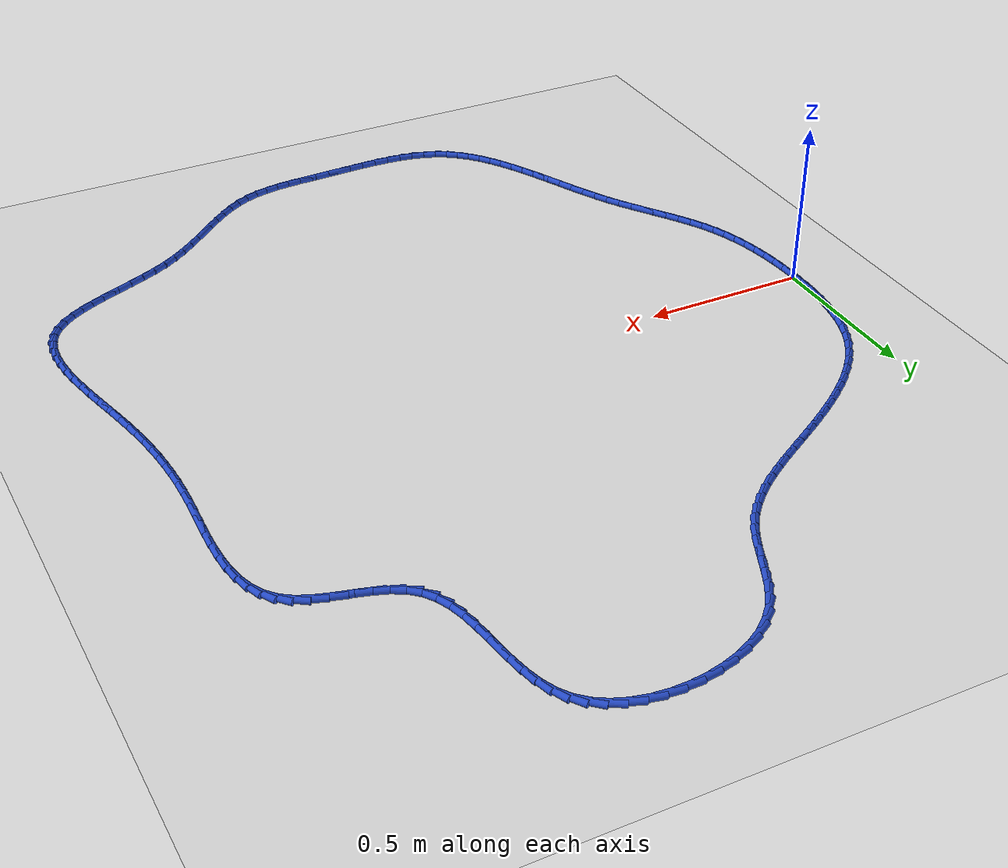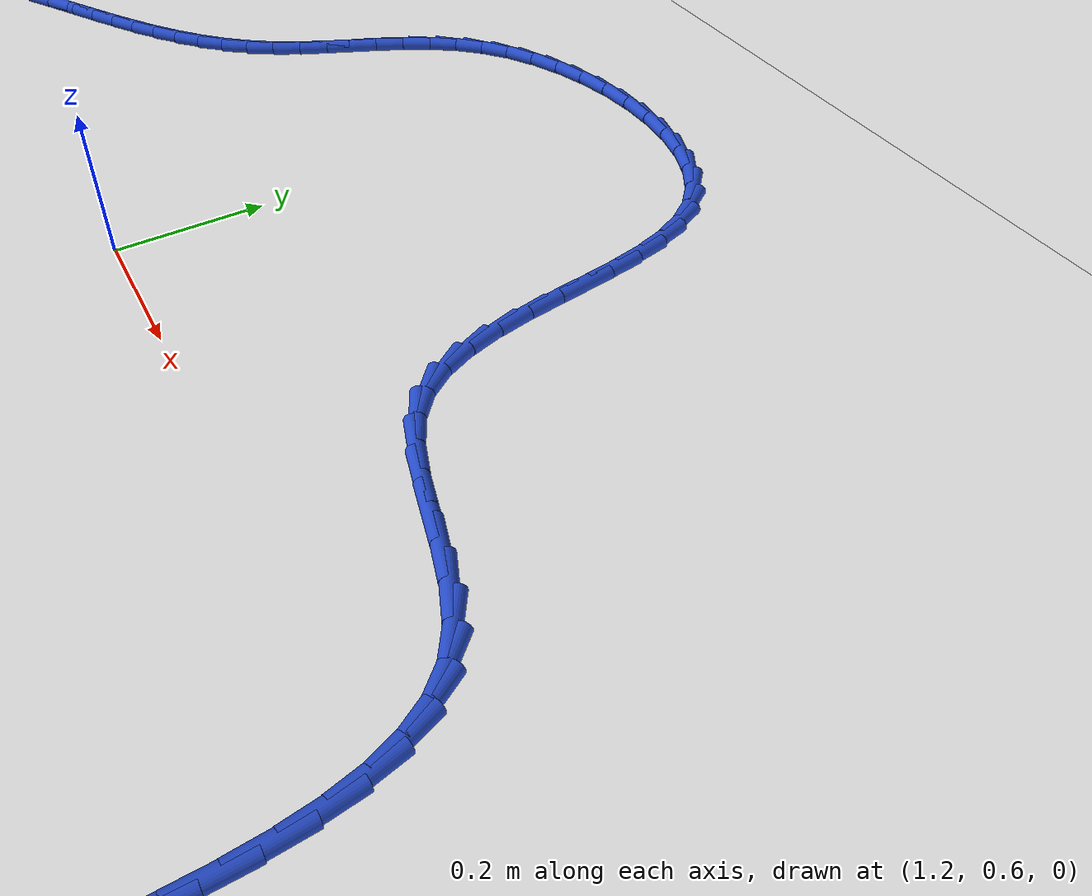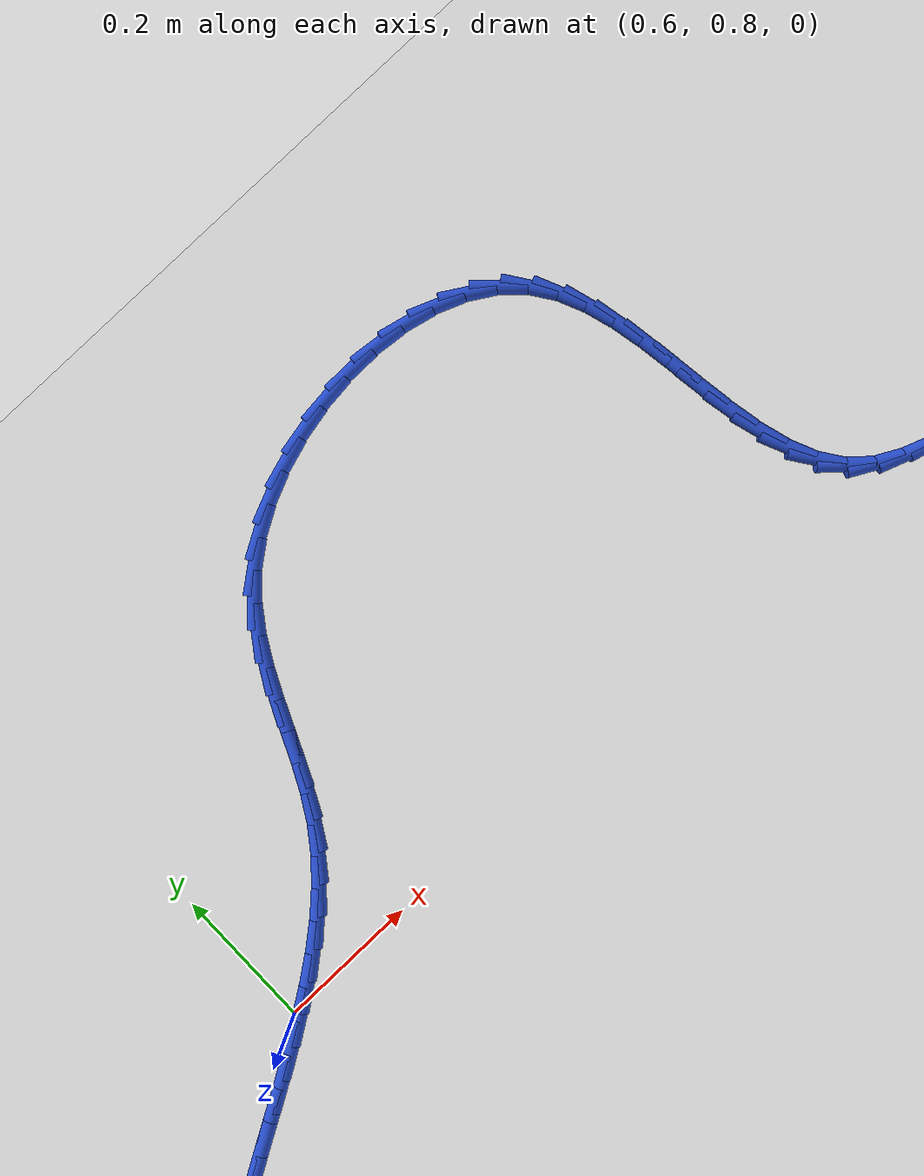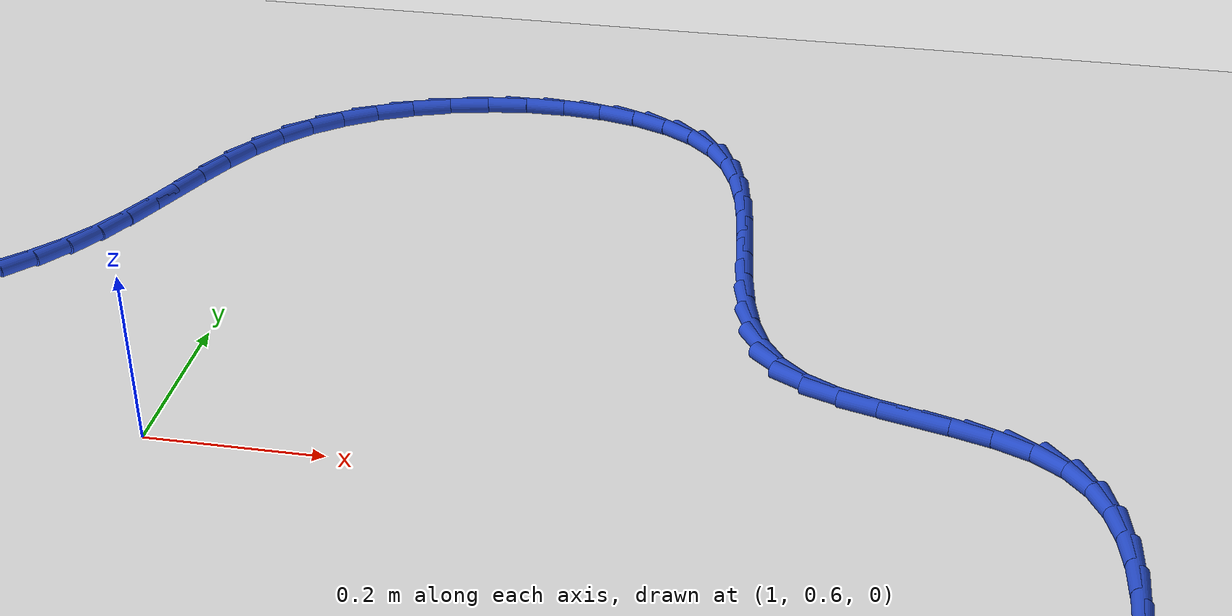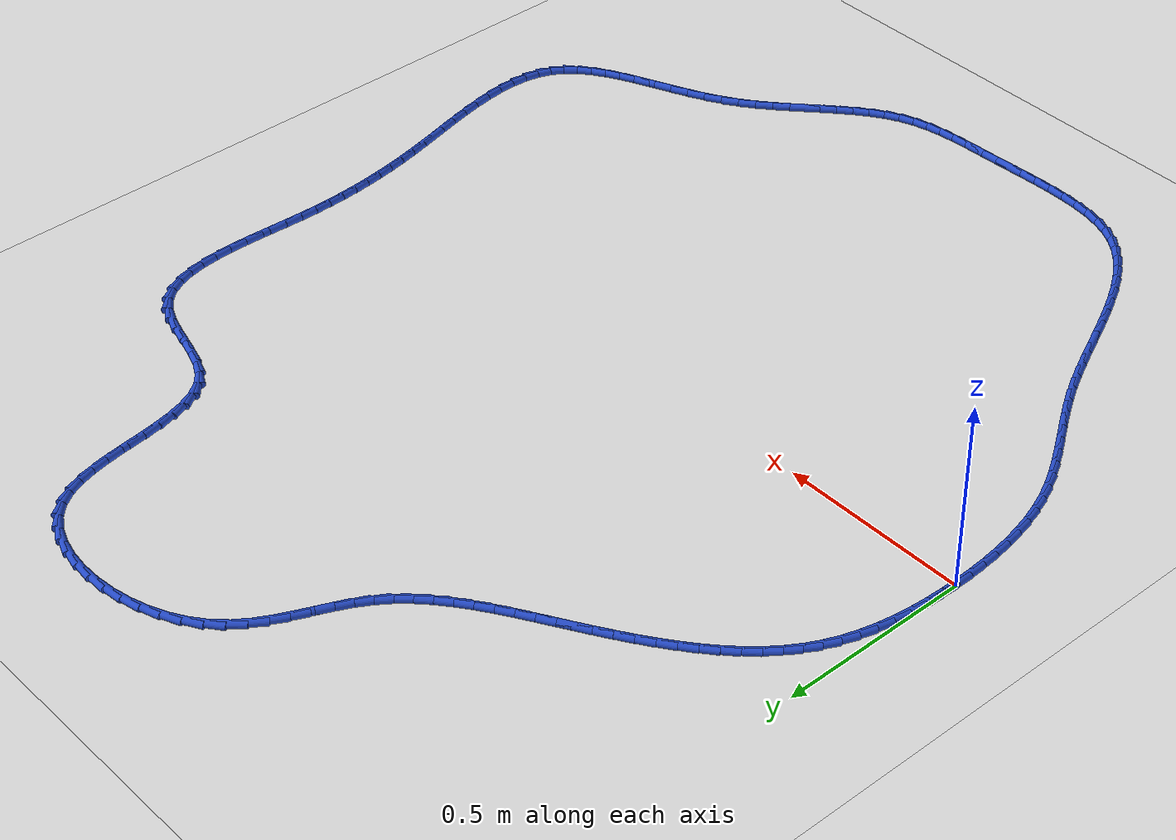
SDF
<sdf version="1.6">
 <world name="default">
  <light name="sun" type="directional">
   <pose>0 0 10 0 -0 0</pose>
   <diffuse>0.8 0.8 0.8 1</diffuse>
   <specular>0.2 0.2 0.2 1</specular>
   <attenuation>
    <range>1000</range>
    <constant>0.9</constant>
    <linear>0.01</linear>
    <quadratic>0.001</quadratic>
   </attenuation>
   <direction>-0.5 0.1 -0.9</direction>
  </light>
  <model name="ground_plane">
   <static>1</static>
   <link name="link">
    <collision name="collision">
     <geometry><plane><normal>0 0 1</normal><size>100 100</size></plane></geometry>
     <surface><friction><ode><mu>100</mu><mu2>50</mu2></ode></friction></surface>
    </collision>
    <visual name="visual">
     <cast_shadows>0</cast_shadows>
     <geometry><plane><normal>0 0 1</normal><size>100 100</size></plane></geometry>
     <material>
      <script><uri>file://media/materials/scripts/gazebo.material</uri><name>Gazebo/WhiteGlow</name></script>
     </material>
    </visual>
   </link>
  </model>
  <gravity>0 0 -9.8</gravity>
  <magnetic_field>6e-06 2.3e-05 -4.2e-05</magnetic_field>
  <atmosphere type="adiabatic"/>
  <physics name="default_physics" default="0" type="ode">
   <max_step_size>0.001</max_step_size>
   <real_time_factor>1</real_time_factor>
   <real_time_update_rate>1000</real_time_update_rate>
  </physics>
  <scene><ambient>0.4 0.4 0.4 1</ambient><background>0.7 0.7 0.7 1</background><shadows>1</shadows></scene>
  <spherical_coordinates>
   <surface_model>EARTH_WGS84</surface_model>
   <latitude_deg>0</latitude_deg>
   <longitude_deg>0</longitude_deg>
   <elevation>0</elevation>
   <heading_deg>0</heading_deg>
  </spherical_coordinates>
  <model name="line">
   <link name="link_0">
    <pose>-9.540979117872439e-18 -9.71445146547012e-17 0.01 0 1.57 1.5653030758352668</pose>
    <collision name="collision">
     <geometry><cylinder><radius>0.01</radius><length>0.08</length></cylinder></geometry>
    </collision>
    <visual name="visual">
     <material>
      <script><name>Gazebo/Blue</name><uri>file://media/materials/scripts/gazebo.material</uri></script>
     </material>
     <geometry><cylinder><radius>0.01</radius><length>0.08</length></cylinder></geometry>
    </visual>
   </link>
   <link name="link_1">
    <pose>0.00025050211197734276 0.04560133773464336 0.01 0 1.57 1.5297810279426987</pose>
    <collision name="collision">
     <geometry><cylinder><radius>0.01</radius><length>0.08</length></cylinder></geometry>
    </collision>
    <visual name="visual">
     <material>
      <script><name>Gazebo/Blue</name><uri>file://media/materials/scripts/gazebo.material</uri></script>
     </material>
     <geometry><cylinder><radius>0.01</radius><length>0.08</length></cylinder></geometry>
    </visual>
   </link>
   <link name="link_2">
    <pose>0.002117362007868992 0.0910919957585255 0.01 0 1.57 1.488524370906503</pose>
    <collision name="collision">
     <geometry><cylinder><radius>0.01</radius><length>0.08</length></cylinder></geometry>
    </collision>
    <visual name="visual">
     <material>
      <script><name>Gazebo/Blue</name><uri>file://media/materials/scripts/gazebo.material</uri></script>
     </material>
     <geometry><cylinder><radius>0.01</radius><length>0.08</length></cylinder></geometry>
    </visual>
   </link>
   <link name="link_3">
    <pose>0.005837761680537417 0.13621067300344877 0.01 0 1.57 1.4409019700494763</pose>
    <collision name="collision">
     <geometry><cylinder><radius>0.01</radius><length>0.08</length></cylinder></geometry>
    </collision>
    <visual name="visual">
     <material>
      <script><name>Gazebo/Blue</name><uri>file://media/materials/scripts/gazebo.material</uri></script>
     </material>
     <geometry><cylinder><radius>0.01</radius><length>0.08</length></cylinder></geometry>
    </visual>
   </link>
   <link name="link_4">
    <pose>0.011648883122845082 0.18069606840121544 0.01 0 1.57 1.3862075633671531</pose>
    <collision name="collision">
     <geometry><cylinder><radius>0.01</radius><length>0.08</length></cylinder></geometry>
    </collision>
    <visual name="visual">
     <material>
      <script><name>Gazebo/Blue</name><uri>file://media/materials/scripts/gazebo.material</uri></script>
     </material>
     <geometry><cylinder><radius>0.01</radius><length>0.08</length></cylinder></geometry>
    </visual>
   </link>
   <link name="link_5">
    <pose>0.019787908327654473 0.22428688088362814 0.01 0 1.57 1.3237033503994662</pose>
    <collision name="collision">
     <geometry><cylinder><radius>0.01</radius><length>0.08</length></cylinder></geometry>
    </collision>
    <visual name="visual">
     <material>
      <script><name>Gazebo/Blue</name><uri>file://media/materials/scripts/gazebo.material</uri></script>
     </material>
     <geometry><cylinder><radius>0.01</radius><length>0.08</length></cylinder></geometry>
    </visual>
   </link>
   <link name="link_6">
    <pose>0.03049201928782805 0.26672180938248913 0.01 0 1.57 1.252696962597922</pose>
    <collision name="collision">
     <geometry><cylinder><radius>0.01</radius><length>0.08</length></cylinder></geometry>
    </collision>
    <visual name="visual">
     <material>
      <script><name>Gazebo/Blue</name><uri>file://media/materials/scripts/gazebo.material</uri></script>
     </material>
     <geometry><cylinder><radius>0.01</radius><length>0.08</length></cylinder></geometry>
    </visual>
   </link>
   <link name="link_7">
    <pose>0.043998397996228275 0.3077395528296009 0.01 0 1.57 1.1726640984225434</pose>
    <collision name="collision">
     <geometry><cylinder><radius>0.01</radius><length>0.08</length></cylinder></geometry>
    </collision>
    <visual name="visual">
     <material>
      <script><name>Gazebo/Blue</name><uri>file://media/materials/scripts/gazebo.material</uri></script>
     </material>
     <geometry><cylinder><radius>0.01</radius><length>0.08</length></cylinder></geometry>
    </visual>
   </link>
   <link name="link_8">
    <pose>0.060544226445717664 0.347078810156766 0.01 0 1.57 1.0840473184928858</pose>
    <collision name="collision">
     <geometry><cylinder><radius>0.01</radius><length>0.08</length></cylinder></geometry>
    </collision>
    <visual name="visual">
     <material>
      <script><name>Gazebo/Blue</name><uri>file://media/materials/scripts/gazebo.material</uri></script>
     </material>
     <geometry><cylinder><radius>0.01</radius><length>0.08</length></cylinder></geometry>
    </visual>
   </link>
   <link name="link_9">
    <pose>0.0803456091846087 0.38449501368439337 0.01 0 1.57 0.9957664719455297</pose>
    <collision name="collision">
     <geometry><cylinder><radius>0.01</radius><length>0.08</length></cylinder></geometry>
    </collision>
    <visual name="visual">
     <material>
      <script><name>Gazebo/Blue</name><uri>file://media/materials/scripts/gazebo.material</uri></script>
     </material>
     <geometry><cylinder><radius>0.01</radius><length>0.08</length></cylinder></geometry>
    </visual>
   </link>
   <link name="link_10">
    <pose>0.10333548296893096 0.4199684027154446 0.01 0 1.57 0.9149621484737105</pose>
    <collision name="collision">
     <geometry><cylinder><radius>0.01</radius><length>0.08</length></cylinder></geometry>
    </collision>
    <visual name="visual">
     <material>
      <script><name>Gazebo/Blue</name><uri>file://media/materials/scripts/gazebo.material</uri></script>
     </material>
     <geometry><cylinder><radius>0.01</radius><length>0.08</length></cylinder></geometry>
    </visual>
   </link>
   <link name="link_11">
    <pose>0.1292441848096846 0.4536400605421592 0.01 0 1.57 0.842478964433634</pose>
    <collision name="collision">
     <geometry><cylinder><radius>0.01</radius><length>0.08</length></cylinder></geometry>
    </collision>
    <visual name="visual">
     <material>
      <script><name>Gazebo/Blue</name><uri>file://media/materials/scripts/gazebo.material</uri></script>
     </material>
     <geometry><cylinder><radius>0.01</radius><length>0.08</length></cylinder></geometry>
    </visual>
   </link>
   <link name="link_12">
    <pose>0.15779765624762143 0.48565456002172885 0.01 0 1.57 0.7785238549478946</pose>
    <collision name="collision">
     <geometry><cylinder><radius>0.01</radius><length>0.08</length></cylinder></geometry>
    </collision>
    <visual name="visual">
     <material>
      <script><name>Gazebo/Blue</name><uri>file://media/materials/scripts/gazebo.material</uri></script>
     </material>
     <geometry><cylinder><radius>0.01</radius><length>0.08</length></cylinder></geometry>
    </visual>
   </link>
   <link name="link_13">
    <pose>0.18872183882349308 0.5161564740113451 0.01 0 1.57 0.7229430882734792</pose>
    <collision name="collision">
     <geometry><cylinder><radius>0.01</radius><length>0.08</length></cylinder></geometry>
    </collision>
    <visual name="visual">
     <material>
      <script><name>Gazebo/Blue</name><uri>file://media/materials/scripts/gazebo.material</uri></script>
     </material>
     <geometry><cylinder><radius>0.01</radius><length>0.08</length></cylinder></geometry>
    </visual>
   </link>
   <link name="link_14">
    <pose>0.22174267407805115 0.5452903753681995 0.01 0 1.57 0.6753656907574038</pose>
    <collision name="collision">
     <geometry><cylinder><radius>0.01</radius><length>0.08</length></cylinder></geometry>
    </collision>
    <visual name="visual">
     <material>
      <script><name>Gazebo/Blue</name><uri>file://media/materials/scripts/gazebo.material</uri></script>
     </material>
     <geometry><cylinder><radius>0.01</radius><length>0.08</length></cylinder></geometry>
    </visual>
   </link>
   <link name="link_15">
    <pose>0.25658610355204736 0.5732008369494833 0.01 0 1.57 0.6353198553763588</pose>
    <collision name="collision">
     <geometry><cylinder><radius>0.01</radius><length>0.08</length></cylinder></geometry>
    </collision>
    <visual name="visual">
     <material>
      <script><name>Gazebo/Blue</name><uri>file://media/materials/scripts/gazebo.material</uri></script>
     </material>
     <geometry><cylinder><radius>0.01</radius><length>0.08</length></cylinder></geometry>
    </visual>
   </link>
   <link name="link_16">
    <pose>0.2929780687862335 0.6000324316123885 0.01 0 1.57 0.6023165751661791</pose>
    <collision name="collision">
     <geometry><cylinder><radius>0.01</radius><length>0.08</length></cylinder></geometry>
    </collision>
    <visual name="visual">
     <material>
      <script><name>Gazebo/Blue</name><uri>file://media/materials/scripts/gazebo.material</uri></script>
     </material>
     <geometry><cylinder><radius>0.01</radius><length>0.08</length></cylinder></geometry>
    </visual>
   </link>
   <link name="link_17">
    <pose>0.3306445113213612 0.6259297322141066 0.01 0 1.57 0.5759045530681607</pose>
    <collision name="collision">
     <geometry><cylinder><radius>0.01</radius><length>0.08</length></cylinder></geometry>
    </collision>
    <visual name="visual">
     <material>
      <script><name>Gazebo/Blue</name><uri>file://media/materials/scripts/gazebo.material</uri></script>
     </material>
     <geometry><cylinder><radius>0.01</radius><length>0.08</length></cylinder></geometry>
    </visual>
   </link>
   <link name="link_18">
    <pose>0.36931137269818193 0.651037311611829 0.01 0 1.57 0.5557038212532415</pose>
    <collision name="collision">
     <geometry><cylinder><radius>0.01</radius><length>0.08</length></cylinder></geometry>
    </collision>
    <visual name="visual">
     <material>
      <script><name>Gazebo/Blue</name><uri>file://media/materials/scripts/gazebo.material</uri></script>
     </material>
     <geometry><cylinder><radius>0.01</radius><length>0.08</length></cylinder></geometry>
    </visual>
   </link>
   <link name="link_19">
    <pose>0.4087045944574477 0.6754997426627473 0.01 0 1.57 0.5414253778234269</pose>
    <collision name="collision">
     <geometry><cylinder><radius>0.01</radius><length>0.08</length></cylinder></geometry>
    </collision>
    <visual name="visual">
     <material>
      <script><name>Gazebo/Blue</name><uri>file://media/materials/scripts/gazebo.material</uri></script>
     </material>
     <geometry><cylinder><radius>0.01</radius><length>0.08</length></cylinder></geometry>
    </visual>
   </link>
   <link name="link_20">
    <pose>0.4485501181399101 0.6994615982240531 0.01 0 1.57 0.5329689783708867</pose>
    <collision name="collision">
     <geometry><cylinder><radius>0.01</radius><length>0.08</length></cylinder></geometry>
    </collision>
    <visual name="visual">
     <material>
      <script><name>Gazebo/Blue</name><uri>file://media/materials/scripts/gazebo.material</uri></script>
     </material>
     <geometry><cylinder><radius>0.01</radius><length>0.08</length></cylinder></geometry>
    </visual>
   </link>
   <link name="link_21">
    <pose>0.4885719016272206 0.7230709365363737 0.01 0 1.57 0.5323891850747435</pose>
    <collision name="collision">
     <geometry><cylinder><radius>0.01</radius><length>0.08</length></cylinder></geometry>
    </collision>
    <visual name="visual">
     <material>
      <script><name>Gazebo/Blue</name><uri>file://media/materials/scripts/gazebo.material</uri></script>
     </material>
     <geometry><cylinder><radius>0.01</radius><length>0.08</length></cylinder></geometry>
    </visual>
   </link>
   <link name="link_22">
    <pose>0.5284451403309848 0.7465614938206808 0.01 0 1.57 0.5420022314829092</pose>
    <collision name="collision">
     <geometry><cylinder><radius>0.01</radius><length>0.08</length></cylinder></geometry>
    </collision>
    <visual name="visual">
     <material>
      <script><name>Gazebo/Blue</name><uri>file://media/materials/scripts/gazebo.material</uri></script>
     </material>
     <geometry><cylinder><radius>0.01</radius><length>0.08</length></cylinder></geometry>
    </visual>
   </link>
   <link name="link_23">
    <pose>0.5677944572105186 0.7702558645032243 0.01 0 1.57 0.5622401183788936</pose>
    <collision name="collision">
     <geometry><cylinder><radius>0.01</radius><length>0.08</length></cylinder></geometry>
    </collision>
    <visual name="visual">
     <material>
      <script><name>Gazebo/Blue</name><uri>file://media/materials/scripts/gazebo.material</uri></script>
     </material>
     <geometry><cylinder><radius>0.01</radius><length>0.08</length></cylinder></geometry>
    </visual>
   </link>
   <link name="link_24">
    <pose>0.6062421294188469 0.7944807647035385 0.01 0 1.57 0.5936302586315509</pose>
    <collision name="collision">
     <geometry><cylinder><radius>0.01</radius><length>0.08</length></cylinder></geometry>
    </collision>
    <visual name="visual">
     <material>
      <script><name>Gazebo/Blue</name><uri>file://media/materials/scripts/gazebo.material</uri></script>
     </material>
     <geometry><cylinder><radius>0.01</radius><length>0.08</length></cylinder></geometry>
    </visual>
   </link>
   <link name="link_25">
    <pose>0.6434104341089945 0.8195629105411578 0.01 0 1.57 0.6368484654022575</pose>
    <collision name="collision">
     <geometry><cylinder><radius>0.01</radius><length>0.08</length></cylinder></geometry>
    </collision>
    <visual name="visual">
     <material>
      <script><name>Gazebo/Blue</name><uri>file://media/materials/scripts/gazebo.material</uri></script>
     </material>
     <geometry><cylinder><radius>0.01</radius><length>0.08</length></cylinder></geometry>
    </visual>
   </link>
   <link name="link_26">
    <pose>0.6789216484339855 0.8458290181356166 0.01 0 1.57 0.6926152212125446</pose>
    <collision name="collision">
     <geometry><cylinder><radius>0.01</radius><length>0.08</length></cylinder></geometry>
    </collision>
    <visual name="visual">
     <material>
      <script><name>Gazebo/Blue</name><uri>file://media/materials/scripts/gazebo.material</uri></script>
     </material>
     <geometry><cylinder><radius>0.01</radius><length>0.08</length></cylinder></geometry>
    </visual>
   </link>
   <link name="link_27">
    <pose>0.7123980495468446 0.8736058036064485 0.01 0 1.57 0.7615112720891524</pose>
    <collision name="collision">
     <geometry><cylinder><radius>0.01</radius><length>0.08</length></cylinder></geometry>
    </collision>
    <visual name="visual">
     <material>
      <script><name>Gazebo/Blue</name><uri>file://media/materials/scripts/gazebo.material</uri></script>
     </material>
     <geometry><cylinder><radius>0.01</radius><length>0.08</length></cylinder></geometry>
    </visual>
   </link>
   <link name="link_28">
    <pose>0.7434619146005969 0.9032199830731887 0.01 0 1.57 0.8436929520012761</pose>
    <collision name="collision">
     <geometry><cylinder><radius>0.01</radius><length>0.08</length></cylinder></geometry>
    </collision>
    <visual name="visual">
     <material>
      <script><name>Gazebo/Blue</name><uri>file://media/materials/scripts/gazebo.material</uri></script>
     </material>
     <geometry><cylinder><radius>0.01</radius><length>0.08</length></cylinder></geometry>
    </visual>
   </link>
   <link name="link_29">
    <pose>0.7717355207482667 0.9349982726553712 0.01 0 1.57 0.9385232051621704</pose>
    <collision name="collision">
     <geometry><cylinder><radius>0.01</radius><length>0.08</length></cylinder></geometry>
    </collision>
    <visual name="visual">
     <material>
      <script><name>Gazebo/Blue</name><uri>file://media/materials/scripts/gazebo.material</uri></script>
     </material>
     <geometry><cylinder><radius>0.01</radius><length>0.08</length></cylinder></geometry>
    </visual>
   </link>
   <link name="link_30">
    <pose>0.796841145142879 0.9692673884725302 0.01 0 1.57 1.0390859069789522</pose>
    <collision name="collision">
     <geometry><cylinder><radius>0.01</radius><length>0.08</length></cylinder></geometry>
    </collision>
    <visual name="visual">
     <material>
      <script><name>Gazebo/Blue</name><uri>file://media/materials/scripts/gazebo.material</uri></script>
     </material>
     <geometry><cylinder><radius>0.01</radius><length>0.08</length></cylinder></geometry>
    </visual>
   </link>
   <link name="link_31">
    <pose>0.8185788586474677 1.0062226554808555 0.01 0 1.57 1.1127757626558452</pose>
    <collision name="collision">
     <geometry><cylinder><radius>0.01</radius><length>0.08</length></cylinder></geometry>
    </collision>
    <visual name="visual">
     <material>
      <script><name>Gazebo/Blue</name><uri>file://media/materials/scripts/gazebo.material</uri></script>
     </material>
     <geometry><cylinder><radius>0.01</radius><length>0.08</length></cylinder></geometry>
    </visual>
   </link>
   <link name="link_32">
    <pose>0.8378255149094231 1.0452636463981777 0.01 0 1.57 1.149328500024085</pose>
    <collision name="collision">
     <geometry><cylinder><radius>0.01</radius><length>0.08</length></cylinder></geometry>
    </collision>
    <visual name="visual">
     <material>
      <script><name>Gazebo/Blue</name><uri>file://media/materials/scripts/gazebo.material</uri></script>
     </material>
     <geometry><cylinder><radius>0.01</radius><length>0.08</length></cylinder></geometry>
    </visual>
   </link>
   <link name="link_33">
    <pose>0.8558612282223872 1.085491920669309 0.01 0 1.57 1.1505495541237387</pose>
    <collision name="collision">
     <geometry><cylinder><radius>0.01</radius><length>0.08</length></cylinder></geometry>
    </collision>
    <visual name="visual">
     <material>
      <script><name>Gazebo/Blue</name><uri>file://media/materials/scripts/gazebo.material</uri></script>
     </material>
     <geometry><cylinder><radius>0.01</radius><length>0.08</length></cylinder></geometry>
    </visual>
   </link>
   <link name="link_34">
    <pose>0.8739668204923616 1.1260085148071128 0.01 0 1.57 1.1171552571898333</pose>
    <collision name="collision">
     <geometry><cylinder><radius>0.01</radius><length>0.08</length></cylinder></geometry>
    </collision>
    <visual name="visual">
     <material>
      <script><name>Gazebo/Blue</name><uri>file://media/materials/scripts/gazebo.material</uri></script>
     </material>
     <geometry><cylinder><radius>0.01</radius><length>0.08</length></cylinder></geometry>
    </visual>
   </link>
   <link name="link_35">
    <pose>0.893423113625348 1.1659144653244524 0.01 0 1.57 1.0487679363123783</pose>
    <collision name="collision">
     <geometry><cylinder><radius>0.01</radius><length>0.08</length></cylinder></geometry>
    </collision>
    <visual name="visual">
     <material>
      <script><name>Gazebo/Blue</name><uri>file://media/materials/scripts/gazebo.material</uri></script>
     </material>
     <geometry><cylinder><radius>0.01</radius><length>0.08</length></cylinder></geometry>
    </visual>
   </link>
   <link name="link_36">
    <pose>0.915510929527348 1.2043108087341912 0.01 0 1.57 0.9451471084817058</pose>
    <collision name="collision">
     <geometry><cylinder><radius>0.01</radius><length>0.08</length></cylinder></geometry>
    </collision>
    <visual name="visual">
     <material>
      <script><name>Gazebo/Blue</name><uri>file://media/materials/scripts/gazebo.material</uri></script>
     </material>
     <geometry><cylinder><radius>0.01</radius><length>0.08</length></cylinder></geometry>
    </visual>
   </link>
   <link name="link_37">
    <pose>0.9415110901043641 1.2402985815491934 0.01 0 1.57 0.8087013914473506</pose>
    <collision name="collision">
     <geometry><cylinder><radius>0.01</radius><length>0.08</length></cylinder></geometry>
    </collision>
    <visual name="visual">
     <material>
      <script><name>Gazebo/Blue</name><uri>file://media/materials/scripts/gazebo.material</uri></script>
     </material>
     <geometry><cylinder><radius>0.01</radius><length>0.08</length></cylinder></geometry>
    </visual>
   </link>
   <link name="link_38">
    <pose>0.9727030356850674 1.272979234341757 0.01 0 1.57 0.6582202324102502</pose>
    <collision name="collision">
     <geometry><cylinder><radius>0.01</radius><length>0.08</length></cylinder></geometry>
    </collision>
    <visual name="visual">
     <material>
      <script><name>Gazebo/Blue</name><uri>file://media/materials/scripts/gazebo.material</uri></script>
     </material>
     <geometry><cylinder><radius>0.01</radius><length>0.08</length></cylinder></geometry>
    </visual>
   </link>
   <link name="link_39">
    <pose>1.009761961641977 1.3016353102078462 0.01 0 1.57 0.5253563533869497</pose>
    <collision name="collision">
     <geometry><cylinder><radius>0.01</radius><length>0.08</length></cylinder></geometry>
    </collision>
    <visual name="visual">
     <material>
      <script><name>Gazebo/Blue</name><uri>file://media/materials/scripts/gazebo.material</uri></script>
     </material>
     <geometry><cylinder><radius>0.01</radius><length>0.08</length></cylinder></geometry>
    </visual>
   </link>
   <link name="link_40">
    <pose>1.0518150176792507 1.326013302325221 0.01 0 1.57 0.40921367634495115</pose>
    <collision name="collision">
     <geometry><cylinder><radius>0.01</radius><length>0.08</length></cylinder></geometry>
    </collision>
    <visual name="visual">
     <material>
      <script><name>Gazebo/Blue</name><uri>file://media/materials/scripts/gazebo.material</uri></script>
     </material>
     <geometry><cylinder><radius>0.01</radius><length>0.08</length></cylinder></geometry>
    </visual>
   </link>
   <link name="link_41">
    <pose>1.097744937931272 1.3459329553434192 0.01 0 1.57 0.30411154297586623</pose>
    <collision name="collision">
     <geometry><cylinder><radius>0.01</radius><length>0.08</length></cylinder></geometry>
    </collision>
    <visual name="visual">
     <material>
      <script><name>Gazebo/Blue</name><uri>file://media/materials/scripts/gazebo.material</uri></script>
     </material>
     <geometry><cylinder><radius>0.01</radius><length>0.08</length></cylinder></geometry>
    </visual>
   </link>
   <link name="link_42">
    <pose>1.1464344565324258 1.3612140139119795 0.01 0 1.57 0.20494608667161407</pose>
    <collision name="collision">
     <geometry><cylinder><radius>0.01</radius><length>0.08</length></cylinder></geometry>
    </collision>
    <visual name="visual">
     <material>
      <script><name>Gazebo/Blue</name><uri>file://media/materials/scripts/gazebo.material</uri></script>
     </material>
     <geometry><cylinder><radius>0.01</radius><length>0.08</length></cylinder></geometry>
    </visual>
   </link>
   <link name="link_43">
    <pose>1.1967663076170973 1.3716762226804409 0.01 0 1.57 0.10701070240283597</pose>
    <collision name="collision">
     <geometry><cylinder><radius>0.01</radius><length>0.08</length></cylinder></geometry>
    </collision>
    <visual name="visual">
     <material>
      <script><name>Gazebo/Blue</name><uri>file://media/materials/scripts/gazebo.material</uri></script>
     </material>
     <geometry><cylinder><radius>0.01</radius><length>0.08</length></cylinder></geometry>
    </visual>
   </link>
   <link name="link_44">
    <pose>1.2476232253196702 1.3771393262983418 0.01 0 1.57 0.005644915793065453</pose>
    <collision name="collision">
     <geometry><cylinder><radius>0.01</radius><length>0.08</length></cylinder></geometry>
    </collision>
    <visual name="visual">
     <material>
      <script><name>Gazebo/Blue</name><uri>file://media/materials/scripts/gazebo.material</uri></script>
     </material>
     <geometry><cylinder><radius>0.01</radius><length>0.08</length></cylinder></geometry>
    </visual>
   </link>
   <link name="link_45">
    <pose>1.2978879437745303 1.3774230694152199 0.01 0 1.57 -0.10415974832302113</pose>
    <collision name="collision">
     <geometry><cylinder><radius>0.01</radius><length>0.08</length></cylinder></geometry>
    </collision>
    <visual name="visual">
     <material>
      <script><name>Gazebo/Blue</name><uri>file://media/materials/scripts/gazebo.material</uri></script>
     </material>
     <geometry><cylinder><radius>0.01</radius><length>0.08</length></cylinder></geometry>
    </visual>
   </link>
   <link name="link_46">
    <pose>1.346443197116061 1.372347196680615 0.01 0 1.57 -0.22810665589423143</pose>
    <collision name="collision">
     <geometry><cylinder><radius>0.01</radius><length>0.08</length></cylinder></geometry>
    </collision>
    <visual name="visual">
     <material>
      <script><name>Gazebo/Blue</name><uri>file://media/materials/scripts/gazebo.material</uri></script>
     </material>
     <geometry><cylinder><radius>0.01</radius><length>0.08</length></cylinder></geometry>
    </visual>
   </link>
   <link name="link_47">
    <pose>1.3921717194786483 1.3617314527440645 0.01 0 1.57 -0.3726847541728337</pose>
    <collision name="collision">
     <geometry><cylinder><radius>0.01</radius><length>0.08</length></cylinder></geometry>
    </collision>
    <visual name="visual">
     <material>
      <script><name>Gazebo/Blue</name><uri>file://media/materials/scripts/gazebo.material</uri></script>
     </material>
     <geometry><cylinder><radius>0.01</radius><length>0.08</length></cylinder></geometry>
    </visual>
   </link>
   <link name="link_48">
    <pose>1.433956244996675 1.3453955822551076 0.01 0 1.57 -0.5444601184396616</pose>
    <collision name="collision">
     <geometry><cylinder><radius>0.01</radius><length>0.08</length></cylinder></geometry>
    </collision>
    <visual name="visual">
     <material>
      <script><name>Gazebo/Blue</name><uri>file://media/materials/scripts/gazebo.material</uri></script>
     </material>
     <geometry><cylinder><radius>0.01</radius><length>0.08</length></cylinder></geometry>
    </visual>
   </link>
   <link name="link_49">
    <pose>1.4706795078045267 1.3231593298632822 0.01 0 1.57 -0.747567374307094</pose>
    <collision name="collision">
     <geometry><cylinder><radius>0.01</radius><length>0.08</length></cylinder></geometry>
    </collision>
    <visual name="visual">
     <material>
      <script><name>Gazebo/Blue</name><uri>file://media/materials/scripts/gazebo.material</uri></script>
     </material>
     <geometry><cylinder><radius>0.01</radius><length>0.08</length></cylinder></geometry>
    </visual>
   </link>
   <link name="link_50">
    <pose>1.5012242420365887 1.2948424402181278 0.01 0 1.57 -0.9692586021782646</pose>
    <collision name="collision">
     <geometry><cylinder><radius>0.01</radius><length>0.08</length></cylinder></geometry>
    </collision>
    <visual name="visual">
     <material>
      <script><name>Gazebo/Blue</name><uri>file://media/materials/scripts/gazebo.material</uri></script>
     </material>
     <geometry><cylinder><radius>0.01</radius><length>0.08</length></cylinder></geometry>
    </visual>
   </link>
   <link name="link_51">
    <pose>1.5248244346616455 1.2604597065780323 0.01 0 1.57 -1.1536797629218414</pose>
    <collision name="collision">
     <geometry><cylinder><radius>0.01</radius><length>0.08</length></cylinder></geometry>
    </collision>
    <visual name="visual">
     <material>
      <script><name>Gazebo/Blue</name><uri>file://media/materials/scripts/gazebo.material</uri></script>
     </material>
     <geometry><cylinder><radius>0.01</radius><length>0.08</length></cylinder></geometry>
    </visual>
   </link>
   <link name="link_52">
    <pose>1.5423410558418746 1.2209293762874835 0.01 0 1.57 -1.2853555912811894</pose>
    <collision name="collision">
     <geometry><cylinder><radius>0.01</radius><length>0.08</length></cylinder></geometry>
    </collision>
    <visual name="visual">
     <material>
      <script><name>Gazebo/Blue</name><uri>file://media/materials/scripts/gazebo.material</uri></script>
     </material>
     <geometry><cylinder><radius>0.01</radius><length>0.08</length></cylinder></geometry>
    </visual>
   </link>
   <link name="link_53">
    <pose>1.5551058110404197 1.1774310932025356 0.01 0 1.57 -1.371587288108067</pose>
    <collision name="collision">
     <geometry><cylinder><radius>0.01</radius><length>0.08</length></cylinder></geometry>
    </collision>
    <visual name="visual">
     <material>
      <script><name>Gazebo/Blue</name><uri>file://media/materials/scripts/gazebo.material</uri></script>
     </material>
     <geometry><cylinder><radius>0.01</radius><length>0.08</length></cylinder></geometry>
    </visual>
   </link>
   <link name="link_54">
    <pose>1.5644504532334635 1.1311445275629504 0.01 0 1.57 -1.4204363894564953</pose>
    <collision name="collision">
     <geometry><cylinder><radius>0.01</radius><length>0.08</length></cylinder></geometry>
    </collision>
    <visual name="visual">
     <material>
      <script><name>Gazebo/Blue</name><uri>file://media/materials/scripts/gazebo.material</uri></script>
     </material>
     <geometry><cylinder><radius>0.01</radius><length>0.08</length></cylinder></geometry>
    </visual>
   </link>
   <link name="link_55">
    <pose>1.571706735397192 1.0832493496084903 0.01 0 1.57 -1.4370970362415991</pose>
    <collision name="collision">
     <geometry><cylinder><radius>0.01</radius><length>0.08</length></cylinder></geometry>
    </collision>
    <visual name="visual">
     <material>
      <script><name>Gazebo/Blue</name><uri>file://media/materials/scripts/gazebo.material</uri></script>
     </material>
     <geometry><cylinder><radius>0.01</radius><length>0.08</length></cylinder></geometry>
    </visual>
   </link>
   <link name="link_56">
    <pose>1.5782064105077882 1.0349252295789189 0.01 0 1.57 -1.4231644895617552</pose>
    <collision name="collision">
     <geometry><cylinder><radius>0.01</radius><length>0.08</length></cylinder></geometry>
    </collision>
    <visual name="visual">
     <material>
      <script><name>Gazebo/Blue</name><uri>file://media/materials/scripts/gazebo.material</uri></script>
     </material>
     <geometry><cylinder><radius>0.01</radius><length>0.08</length></cylinder></geometry>
    </visual>
   </link>
   <link name="link_57">
    <pose>1.5852812315414362 0.9873518377139976 0.01 0 1.57 -1.37649689555462</pose>
    <collision name="collision">
     <geometry><cylinder><radius>0.01</radius><length>0.08</length></cylinder></geometry>
    </collision>
    <visual name="visual">
     <material>
      <script><name>Gazebo/Blue</name><uri>file://media/materials/scripts/gazebo.material</uri></script>
     </material>
     <geometry><cylinder><radius>0.01</radius><length>0.08</length></cylinder></geometry>
    </visual>
   </link>
   <link name="link_58">
    <pose>1.5942629514743198 0.9417088442534889 0.01 0 1.57 -1.2910168562740298</pose>
    <collision name="collision">
     <geometry><cylinder><radius>0.01</radius><length>0.08</length></cylinder></geometry>
    </collision>
    <visual name="visual">
     <material>
      <script><name>Gazebo/Blue</name><uri>file://media/materials/scripts/gazebo.material</uri></script>
     </material>
     <geometry><cylinder><radius>0.01</radius><length>0.08</length></cylinder></geometry>
    </visual>
   </link>
   <link name="link_59">
    <pose>1.606483323282623 0.8991759194371558 0.01 0 1.57 -1.1570833213207852</pose>
    <collision name="collision">
     <geometry><cylinder><radius>0.01</radius><length>0.08</length></cylinder></geometry>
    </collision>
    <visual name="visual">
     <material>
      <script><name>Gazebo/Blue</name><uri>file://media/materials/scripts/gazebo.material</uri></script>
     </material>
     <geometry><cylinder><radius>0.01</radius><length>0.08</length></cylinder></geometry>
    </visual>
   </link>
   <link name="link_60">
    <pose>1.6232740999425301 0.8609327335047606 0.01 0 1.57 -0.9651816054771756</pose>
    <collision name="collision">
     <geometry><cylinder><radius>0.01</radius><length>0.08</length></cylinder></geometry>
    </collision>
    <visual name="visual">
     <material>
      <script><name>Gazebo/Blue</name><uri>file://media/materials/scripts/gazebo.material</uri></script>
     </material>
     <geometry><cylinder><radius>0.01</radius><length>0.08</length></cylinder></geometry>
    </visual>
   </link>
   <link name="link_61">
    <pose>1.6459670344302255 0.8281589566960654 0.01 0 1.57 -0.718427338330417</pose>
    <collision name="collision">
     <geometry><cylinder><radius>0.01</radius><length>0.08</length></cylinder></geometry>
    </collision>
    <visual name="visual">
     <material>
      <script><name>Gazebo/Blue</name><uri>file://media/materials/scripts/gazebo.material</uri></script>
     </material>
     <geometry><cylinder><radius>0.01</radius><length>0.08</length></cylinder></geometry>
    </visual>
   </link>
   <link name="link_62">
    <pose>1.675871255263682 0.802014016351121 0.01 0 1.57 -0.4854694153423226</pose>
    <collision name="collision">
     <geometry><cylinder><radius>0.01</radius><length>0.08</length></cylinder></geometry>
    </collision>
    <visual name="visual">
     <material>
      <script><name>Gazebo/Blue</name><uri>file://media/materials/scripts/gazebo.material</uri></script>
     </material>
     <geometry><cylinder><radius>0.01</radius><length>0.08</length></cylinder></geometry>
    </visual>
   </link>
   <link name="link_63">
    <pose>1.7129491510441903 0.7824523641673301 0.01 0 1.57 -0.33962554845911647</pose>
    <collision name="collision">
     <geometry><cylinder><radius>0.01</radius><length>0.08</length></cylinder></geometry>
    </collision>
    <visual name="visual">
     <material>
      <script><name>Gazebo/Blue</name><uri>file://media/materials/scripts/gazebo.material</uri></script>
     </material>
     <geometry><cylinder><radius>0.01</radius><length>0.08</length></cylinder></geometry>
    </visual>
   </link>
   <link name="link_64">
    <pose>1.75508180860347 0.7675662378345782 0.01 0 1.57 -0.26698039380904803</pose>
    <collision name="collision">
     <geometry><cylinder><radius>0.01</radius><length>0.08</length></cylinder></geometry>
    </collision>
    <visual name="visual">
     <material>
      <script><name>Gazebo/Blue</name><uri>file://media/materials/scripts/gazebo.material</uri></script>
     </material>
     <geometry><cylinder><radius>0.01</radius><length>0.08</length></cylinder></geometry>
    </visual>
   </link>
   <link name="link_65">
    <pose>1.7999719943619998 0.755288325489439 0.01 0 1.57 -0.2532500357515321</pose>
    <collision name="collision">
     <geometry><cylinder><radius>0.01</radius><length>0.08</length></cylinder></geometry>
    </collision>
    <visual name="visual">
     <material>
      <script><name>Gazebo/Blue</name><uri>file://media/materials/scripts/gazebo.material</uri></script>
     </material>
     <geometry><cylinder><radius>0.01</radius><length>0.08</length></cylinder></geometry>
    </visual>
   </link>
   <link name="link_66">
    <pose>1.8453224747402575 0.7435513152684852 0.01 0 1.57 -0.29586498274814405</pose>
    <collision name="collision">
     <geometry><cylinder><radius>0.01</radius><length>0.08</length></cylinder></geometry>
    </collision>
    <visual name="visual">
     <material>
      <script><name>Gazebo/Blue</name><uri>file://media/materials/scripts/gazebo.material</uri></script>
     </material>
     <geometry><cylinder><radius>0.01</radius><length>0.08</length></cylinder></geometry>
    </visual>
   </link>
   <link name="link_67">
    <pose>1.8888360161587199 0.7302878953082907 0.01 0 1.57 -0.4044684133384725</pose>
    <collision name="collision">
     <geometry><cylinder><radius>0.01</radius><length>0.08</length></cylinder></geometry>
    </collision>
    <visual name="visual">
     <material>
      <script><name>Gazebo/Blue</name><uri>file://media/materials/scripts/gazebo.material</uri></script>
     </material>
     <geometry><cylinder><radius>0.01</radius><length>0.08</length></cylinder></geometry>
    </visual>
   </link>
   <link name="link_68">
    <pose>1.9282153850378656 0.7134307537454287 0.01 0 1.57 -0.5980825358300854</pose>
    <collision name="collision">
     <geometry><cylinder><radius>0.01</radius><length>0.08</length></cylinder></geometry>
    </collision>
    <visual name="visual">
     <material>
      <script><name>Gazebo/Blue</name><uri>file://media/materials/scripts/gazebo.material</uri></script>
     </material>
     <geometry><cylinder><radius>0.01</radius><length>0.08</length></cylinder></geometry>
    </visual>
   </link>
   <link name="link_69">
    <pose>1.961206890911982 0.6909527971176379 0.01 0 1.57 -0.8424765588874689</pose>
    <collision name="collision">
     <geometry><cylinder><radius>0.01</radius><length>0.08</length></cylinder></geometry>
    </collision>
    <visual name="visual">
     <material>
      <script><name>Gazebo/Blue</name><uri>file://media/materials/scripts/gazebo.material</uri></script>
     </material>
     <geometry><cylinder><radius>0.01</radius><length>0.08</length></cylinder></geometry>
    </visual>
   </link>
   <link name="link_70">
    <pose>1.9869381336148886 0.6621027545332306 0.01 0 1.57 -1.0618483826395952</pose>
    <collision name="collision">
     <geometry><cylinder><radius>0.01</radius><length>0.08</length></cylinder></geometry>
    </collision>
    <visual name="visual">
     <material>
      <script><name>Gazebo/Blue</name><uri>file://media/materials/scripts/gazebo.material</uri></script>
     </material>
     <geometry><cylinder><radius>0.01</radius><length>0.08</length></cylinder></geometry>
    </visual>
   </link>
   <link name="link_71">
    <pose>2.0061691791102474 0.6276371750966879 0.01 0 1.57 -1.2374858874184937</pose>
    <collision name="collision">
     <geometry><cylinder><radius>0.01</radius><length>0.08</length></cylinder></geometry>
    </collision>
    <visual name="visual">
     <material>
      <script><name>Gazebo/Blue</name><uri>file://media/materials/scripts/gazebo.material</uri></script>
     </material>
     <geometry><cylinder><radius>0.01</radius><length>0.08</length></cylinder></geometry>
    </visual>
   </link>
   <link name="link_72">
    <pose>2.019754311623581 0.5883996321861614 0.01 0 1.57 -1.3698322019591416</pose>
    <collision name="collision">
     <geometry><cylinder><radius>0.01</radius><length>0.08</length></cylinder></geometry>
    </collision>
    <visual name="visual">
     <material>
      <script><name>Gazebo/Blue</name><uri>file://media/materials/scripts/gazebo.material</uri></script>
     </material>
     <geometry><cylinder><radius>0.01</radius><length>0.08</length></cylinder></geometry>
    </visual>
   </link>
   <link name="link_73">
    <pose>2.0285478153804126 0.5452336991798011 0.01 0 1.57 -1.4661832939021022</pose>
    <collision name="collision">
     <geometry><cylinder><radius>0.01</radius><length>0.08</length></cylinder></geometry>
    </collision>
    <visual name="visual">
     <material>
      <script><name>Gazebo/Blue</name><uri>file://media/materials/scripts/gazebo.material</uri></script>
     </material>
     <geometry><cylinder><radius>0.01</radius><length>0.08</length></cylinder></geometry>
    </visual>
   </link>
   <link name="link_74">
    <pose>2.0334039746062644 0.49898294945575783 0.01 0 1.57 -1.5342478320699626</pose>
    <collision name="collision">
     <geometry><cylinder><radius>0.01</radius><length>0.08</length></cylinder></geometry>
    </collision>
    <visual name="visual">
     <material>
      <script><name>Gazebo/Blue</name><uri>file://media/materials/scripts/gazebo.material</uri></script>
     </material>
     <geometry><cylinder><radius>0.01</radius><length>0.08</length></cylinder></geometry>
    </visual>
   </link>
   <link name="link_75">
    <pose>2.0351770735266594 0.4504909563921833 0.01 0 1.57 1.561662881888584</pose>
    <collision name="collision">
     <geometry><cylinder><radius>0.01</radius><length>0.08</length></cylinder></geometry>
    </collision>
    <visual name="visual">
     <material>
      <script><name>Gazebo/Blue</name><uri>file://media/materials/scripts/gazebo.material</uri></script>
     </material>
     <geometry><cylinder><radius>0.01</radius><length>0.08</length></cylinder></geometry>
    </visual>
   </link>
   <link name="link_76">
    <pose>2.034721396367121 0.4006012933672278 0.01 0 1.57 1.5345308576602859</pose>
    <collision name="collision">
     <geometry><cylinder><radius>0.01</radius><length>0.08</length></cylinder></geometry>
    </collision>
    <visual name="visual">
     <material>
      <script><name>Gazebo/Blue</name><uri>file://media/materials/scripts/gazebo.material</uri></script>
     </material>
     <geometry><cylinder><radius>0.01</radius><length>0.08</length></cylinder></geometry>
    </visual>
   </link>
   <link name="link_77">
    <pose>2.0328912273531716 0.3501575337590418 0.01 0 1.57 1.523967657459502</pose>
    <collision name="collision">
     <geometry><cylinder><radius>0.01</radius><length>0.08</length></cylinder></geometry>
    </collision>
    <visual name="visual">
     <material>
      <script><name>Gazebo/Blue</name><uri>file://media/materials/scripts/gazebo.material</uri></script>
     </material>
     <geometry><cylinder><radius>0.01</radius><length>0.08</length></cylinder></geometry>
    </visual>
   </link>
   <link name="link_78">
    <pose>2.0305408507103344 0.30000325094577696 0.01 0 1.57 1.5296883405127977</pose>
    <collision name="collision">
     <geometry><cylinder><radius>0.01</radius><length>0.08</length></cylinder></geometry>
    </collision>
    <visual name="visual">
     <material>
      <script><name>Gazebo/Blue</name><uri>file://media/materials/scripts/gazebo.material</uri></script>
     </material>
     <geometry><cylinder><radius>0.01</radius><length>0.08</length></cylinder></geometry>
    </visual>
   </link>
   <link name="link_79">
    <pose>2.028524550664132 0.25098201830558337 0.01 0 1.57 1.5510472717668295</pose>
    <collision name="collision">
     <geometry><cylinder><radius>0.01</radius><length>0.08</length></cylinder></geometry>
    </collision>
    <visual name="visual">
     <material>
      <script><name>Gazebo/Blue</name><uri>file://media/materials/scripts/gazebo.material</uri></script>
     </material>
     <geometry><cylinder><radius>0.01</radius><length>0.08</length></cylinder></geometry>
    </visual>
   </link>
   <link name="link_80">
    <pose>2.027592484786448 0.20379268712882578 0.01 0 1.57 -1.5634307403786163</pose>
    <collision name="collision">
     <geometry><cylinder><radius>0.01</radius><length>0.08</length></cylinder></geometry>
    </collision>
    <visual name="visual">
     <material>
      <script><name>Gazebo/Blue</name><uri>file://media/materials/scripts/gazebo.material</uri></script>
     </material>
     <geometry><cylinder><radius>0.01</radius><length>0.08</length></cylinder></geometry>
    </visual>
   </link>
   <link name="link_81">
    <pose>2.027927237802748 0.1583452585466351 0.01 0 1.57 -1.5346882577186678</pose>
    <collision name="collision">
     <geometry><cylinder><radius>0.01</radius><length>0.08</length></cylinder></geometry>
    </collision>
    <visual name="visual">
     <material>
      <script><name>Gazebo/Blue</name><uri>file://media/materials/scripts/gazebo.material</uri></script>
     </material>
     <geometry><cylinder><radius>0.01</radius><length>0.08</length></cylinder></geometry>
    </visual>
   </link>
   <link name="link_82">
    <pose>2.029518958907003 0.11428227410213897 0.01 0 1.57 -1.5049314027583296</pose>
    <collision name="collision">
     <geometry><cylinder><radius>0.01</radius><length>0.08</length></cylinder></geometry>
    </collision>
    <visual name="visual">
     <material>
      <script><name>Gazebo/Blue</name><uri>file://media/materials/scripts/gazebo.material</uri></script>
     </material>
     <geometry><cylinder><radius>0.01</radius><length>0.08</length></cylinder></geometry>
    </visual>
   </link>
   <link name="link_83">
    <pose>2.0323576420128533 0.07124605951962862 0.01 0 1.57 -1.4748932689569254</pose>
    <collision name="collision">
     <geometry><cylinder><radius>0.01</radius><length>0.08</length></cylinder></geometry>
    </collision>
    <visual name="visual">
     <material>
      <script><name>Gazebo/Blue</name><uri>file://media/materials/scripts/gazebo.material</uri></script>
     </material>
     <geometry><cylinder><radius>0.01</radius><length>0.08</length></cylinder></geometry>
    </visual>
   </link>
   <link name="link_84">
    <pose>2.0364332810339403 0.02887894052339354 0.01 0 1.57 -1.445373256375543</pose>
    <collision name="collision">
     <geometry><cylinder><radius>0.01</radius><length>0.08</length></cylinder></geometry>
    </collision>
    <visual name="visual">
     <material>
      <script><name>Gazebo/Blue</name><uri>file://media/materials/scripts/gazebo.material</uri></script>
     </material>
     <geometry><cylinder><radius>0.01</radius><length>0.08</length></cylinder></geometry>
    </visual>
   </link>
   <link name="link_85">
    <pose>2.0417358698839037 -0.013176757162275163 0.01 0 1.57 -1.4171654546028096</pose>
    <collision name="collision">
     <geometry><cylinder><radius>0.01</radius><length>0.08</length></cylinder></geometry>
    </collision>
    <visual name="visual">
     <material>
      <script><name>Gazebo/Blue</name><uri>file://media/materials/scripts/gazebo.material</uri></script>
     </material>
     <geometry><cylinder><radius>0.01</radius><length>0.08</length></cylinder></geometry>
    </visual>
   </link>
   <link name="link_86">
    <pose>2.0482554024763844 -0.055278707813087594 0.01 0 1.57 -1.3909854404566688</pose>
    <collision name="collision">
     <geometry><cylinder><radius>0.01</radius><length>0.08</length></cylinder></geometry>
    </collision>
    <visual name="visual">
     <material>
      <script><name>Gazebo/Blue</name><uri>file://media/materials/scripts/gazebo.material</uri></script>
     </material>
     <geometry><cylinder><radius>0.01</radius><length>0.08</length></cylinder></geometry>
    </visual>
   </link>
   <link name="link_87">
    <pose>2.055981872725024 -0.09778458570475346 0.01 0 1.57 -1.3674098730765814</pose>
    <collision name="collision">
     <geometry><cylinder><radius>0.01</radius><length>0.08</length></cylinder></geometry>
    </collision>
    <visual name="visual">
     <material>
      <script><name>Gazebo/Blue</name><uri>file://media/materials/scripts/gazebo.material</uri></script>
     </material>
     <geometry><cylinder><radius>0.01</radius><length>0.08</length></cylinder></geometry>
    </visual>
   </link>
   <link name="link_88">
    <pose>2.064905274543462 -0.14105206511298232 0.01 0 1.57 -1.3468393014528395</pose>
    <collision name="collision">
     <geometry><cylinder><radius>0.01</radius><length>0.08</length></cylinder></geometry>
    </collision>
    <visual name="visual">
     <material>
      <script><name>Gazebo/Blue</name><uri>file://media/materials/scripts/gazebo.material</uri></script>
     </material>
     <geometry><cylinder><radius>0.01</radius><length>0.08</length></cylinder></geometry>
    </visual>
   </link>
   <link name="link_89">
    <pose>2.075015601845341 -0.1854388203134849 0.01 0 1.57 -1.3303079527624582</pose>
    <collision name="collision">
     <geometry><cylinder><radius>0.01</radius><length>0.08</length></cylinder></geometry>
    </collision>
    <visual name="visual">
     <material>
      <script><name>Gazebo/Blue</name><uri>file://media/materials/scripts/gazebo.material</uri></script>
     </material>
     <geometry><cylinder><radius>0.01</radius><length>0.08</length></cylinder></geometry>
    </visual>
   </link>
   <link name="link_90">
    <pose>2.0862450507410677 -0.23122949877129095 0.01 0 1.57 -1.3234082910188119</pose>
    <collision name="collision">
     <geometry><cylinder><radius>0.01</radius><length>0.08</length></cylinder></geometry>
    </collision>
    <visual name="visual">
     <material>
      <script><name>Gazebo/Blue</name><uri>file://media/materials/scripts/gazebo.material</uri></script>
     </material>
     <geometry><cylinder><radius>0.01</radius><length>0.08</length></cylinder></geometry>
    </visual>
   </link>
   <link name="link_91">
    <pose>2.098100880559092 -0.27817184557468294 0.01 0 1.57 -1.3278091539093344</pose>
    <collision name="collision">
     <geometry><cylinder><radius>0.01</radius><length>0.08</length></cylinder></geometry>
    </collision>
    <visual name="visual">
     <material>
      <script><name>Gazebo/Blue</name><uri>file://media/materials/scripts/gazebo.material</uri></script>
     </material>
     <geometry><cylinder><radius>0.01</radius><length>0.08</length></cylinder></geometry>
    </visual>
   </link>
   <link name="link_92">
    <pose>2.1099007599251283 -0.32577406030016526 0.01 0 1.57 -1.3432609018694313</pose>
    <collision name="collision">
     <geometry><cylinder><radius>0.01</radius><length>0.08</length></cylinder></geometry>
    </collision>
    <visual name="visual">
     <material>
      <script><name>Gazebo/Blue</name><uri>file://media/materials/scripts/gazebo.material</uri></script>
     </material>
     <geometry><cylinder><radius>0.01</radius><length>0.08</length></cylinder></geometry>
    </visual>
   </link>
   <link name="link_93">
    <pose>2.1209614815974667 -0.3735432358765666 0.01 0 1.57 -1.370368405681729</pose>
    <collision name="collision">
     <geometry><cylinder><radius>0.01</radius><length>0.08</length></cylinder></geometry>
    </collision>
    <visual name="visual">
     <material>
      <script><name>Gazebo/Blue</name><uri>file://media/materials/scripts/gazebo.material</uri></script>
     </material>
     <geometry><cylinder><radius>0.01</radius><length>0.08</length></cylinder></geometry>
    </visual>
   </link>
   <link name="link_94">
    <pose>2.1305998383343985 -0.4209864652327167 0.01 0 1.57 -1.410617232083481</pose>
    <collision name="collision">
     <geometry><cylinder><radius>0.01</radius><length>0.08</length></cylinder></geometry>
    </collision>
    <visual name="visual">
     <material>
      <script><name>Gazebo/Blue</name><uri>file://media/materials/scripts/gazebo.material</uri></script>
     </material>
     <geometry><cylinder><radius>0.01</radius><length>0.08</length></cylinder></geometry>
    </visual>
   </link>
   <link name="link_95">
    <pose>2.1381326228942132 -0.46761084129744257 0.01 0 1.57 -1.4664813344148746</pose>
    <collision name="collision">
     <geometry><cylinder><radius>0.01</radius><length>0.08</length></cylinder></geometry>
    </collision>
    <visual name="visual">
     <material>
      <script><name>Gazebo/Blue</name><uri>file://media/materials/scripts/gazebo.material</uri></script>
     </material>
     <geometry><cylinder><radius>0.01</radius><length>0.08</length></cylinder></geometry>
    </visual>
   </link>
   <link name="link_96">
    <pose>2.1428766280352023 -0.5129234569995738 0.01 0 1.57 -1.54156819058583</pose>
    <collision name="collision">
     <geometry><cylinder><radius>0.01</radius><length>0.08</length></cylinder></geometry>
    </collision>
    <visual name="visual">
     <material>
      <script><name>Gazebo/Blue</name><uri>file://media/materials/scripts/gazebo.material</uri></script>
     </material>
     <geometry><cylinder><radius>0.01</radius><length>0.08</length></cylinder></geometry>
    </visual>
   </link>
   <link name="link_97">
    <pose>2.144148646515654 -0.5564314052679391 0.01 0 1.57 1.5009477716565451</pose>
    <collision name="collision">
     <geometry><cylinder><radius>0.01</radius><length>0.08</length></cylinder></geometry>
    </collision>
    <visual name="visual">
     <material>
      <script><name>Gazebo/Blue</name><uri>file://media/materials/scripts/gazebo.material</uri></script>
     </material>
     <geometry><cylinder><radius>0.01</radius><length>0.08</length></cylinder></geometry>
    </visual>
   </link>
   <link name="link_98">
    <pose>2.14126547109386 -0.5976417790313673 0.01 0 1.57 1.3724599721803166</pose>
    <collision name="collision">
     <geometry><cylinder><radius>0.01</radius><length>0.08</length></cylinder></geometry>
    </collision>
    <visual name="visual">
     <material>
      <script><name>Gazebo/Blue</name><uri>file://media/materials/scripts/gazebo.material</uri></script>
     </material>
     <geometry><cylinder><radius>0.01</radius><length>0.08</length></cylinder></geometry>
    </visual>
   </link>
   <link name="link_99">
    <pose>2.1335438945281116 -0.636061671218688 0.01 0 1.57 1.210355044194364</pose>
    <collision name="collision">
     <geometry><cylinder><radius>0.01</radius><length>0.08</length></cylinder></geometry>
    </collision>
    <visual name="visual">
     <material>
      <script><name>Gazebo/Blue</name><uri>file://media/materials/scripts/gazebo.material</uri></script>
     </material>
     <geometry><cylinder><radius>0.01</radius><length>0.08</length></cylinder></geometry>
    </visual>
   </link>
   <link name="link_100">
    <pose>2.1203007095766977 -0.6711981747587286 0.01 0 1.57 1.0178724397566041</pose>
    <collision name="collision">
     <geometry><cylinder><radius>0.01</radius><length>0.08</length></cylinder></geometry>
    </collision>
    <visual name="visual">
     <material>
      <script><name>Gazebo/Blue</name><uri>file://media/materials/scripts/gazebo.material</uri></script>
     </material>
     <geometry><cylinder><radius>0.01</radius><length>0.08</length></cylinder></geometry>
    </visual>
   </link>
   <link name="link_101">
    <pose>2.1009178081854722 -0.7026060323657657 0.01 0 1.57 0.8330869957607425</pose>
    <collision name="collision">
     <geometry><cylinder><radius>0.01</radius><length>0.08</length></cylinder></geometry>
    </collision>
    <visual name="visual">
     <material>
      <script><name>Gazebo/Blue</name><uri>file://media/materials/scripts/gazebo.material</uri></script>
     </material>
     <geometry><cylinder><radius>0.01</radius><length>0.08</length></cylinder></geometry>
    </visual>
   </link>
   <link name="link_102">
    <pose>2.0756104852558335 -0.7304500016176918 0.01 0 1.57 0.6849679642949923</pose>
    <collision name="collision">
     <geometry><cylinder><radius>0.01</radius><length>0.08</length></cylinder></geometry>
    </collision>
    <visual name="visual">
     <material>
      <script><name>Gazebo/Blue</name><uri>file://media/materials/scripts/gazebo.material</uri></script>
     </material>
     <geometry><cylinder><radius>0.01</radius><length>0.08</length></cylinder></geometry>
    </visual>
   </link>
   <link name="link_103">
    <pose>2.0451704880897026 -0.7553167782798591 0.01 0 1.57 0.5740381628270436</pose>
    <collision name="collision">
     <geometry><cylinder><radius>0.01</radius><length>0.08</length></cylinder></geometry>
    </collision>
    <visual name="visual">
     <material>
      <script><name>Gazebo/Blue</name><uri>file://media/materials/scripts/gazebo.material</uri></script>
     </material>
     <geometry><cylinder><radius>0.01</radius><length>0.08</length></cylinder></geometry>
    </visual>
   </link>
   <link name="link_104">
    <pose>2.010401073939839 -0.7778014829030674 0.01 0 1.57 0.4954999983153783</pose>
    <collision name="collision">
     <geometry><cylinder><radius>0.01</radius><length>0.08</length></cylinder></geometry>
    </collision>
    <visual name="visual">
     <material>
      <script><name>Gazebo/Blue</name><uri>file://media/materials/scripts/gazebo.material</uri></script>
     </material>
     <geometry><cylinder><radius>0.01</radius><length>0.08</length></cylinder></geometry>
    </visual>
   </link>
   <link name="link_105">
    <pose>1.972105500059005 -0.7984992360381156 0.01 0 1.57 0.44388875521024784</pose>
    <collision name="collision">
     <geometry><cylinder><radius>0.01</radius><length>0.08</length></cylinder></geometry>
    </collision>
    <visual name="visual">
     <material>
      <script><name>Gazebo/Blue</name><uri>file://media/materials/scripts/gazebo.material</uri></script>
     </material>
     <geometry><cylinder><radius>0.01</radius><length>0.08</length></cylinder></geometry>
    </visual>
   </link>
   <link name="link_106">
    <pose>1.931087023699962 -0.818005158235804 0.01 0 1.57 0.4148275710094729</pose>
    <collision name="collision">
     <geometry><cylinder><radius>0.01</radius><length>0.08</length></cylinder></geometry>
    </collision>
    <visual name="visual">
     <material>
      <script><name>Gazebo/Blue</name><uri>file://media/materials/scripts/gazebo.material</uri></script>
     </material>
     <geometry><cylinder><radius>0.01</radius><length>0.08</length></cylinder></geometry>
    </visual>
   </link>
   <link name="link_107">
    <pose>1.88814890211547 -0.8369143700469324 0.01 0 1.57 0.40541170640071145</pose>
    <collision name="collision">
     <geometry><cylinder><radius>0.01</radius><length>0.08</length></cylinder></geometry>
    </collision>
    <visual name="visual">
     <material>
      <script><name>Gazebo/Blue</name><uri>file://media/materials/scripts/gazebo.material</uri></script>
     </material>
     <geometry><cylinder><radius>0.01</radius><length>0.08</length></cylinder></geometry>
    </visual>
   </link>
   <link name="link_108">
    <pose>1.8440943925582902 -0.8558219920223002 0.01 0 1.57 0.4141176441495928</pose>
    <collision name="collision">
     <geometry><cylinder><radius>0.01</radius><length>0.08</length></cylinder></geometry>
    </collision>
    <visual name="visual">
     <material>
      <script><name>Gazebo/Blue</name><uri>file://media/materials/scripts/gazebo.material</uri></script>
     </material>
     <geometry><cylinder><radius>0.01</radius><length>0.08</length></cylinder></geometry>
    </visual>
   </link>
   <link name="link_109">
    <pose>1.7997267522811833 -0.8753231447127077 0.01 0 1.57 0.4406177958118638</pose>
    <collision name="collision">
     <geometry><cylinder><radius>0.01</radius><length>0.08</length></cylinder></geometry>
    </collision>
    <visual name="visual">
     <material>
      <script><name>Gazebo/Blue</name><uri>file://media/materials/scripts/gazebo.material</uri></script>
     </material>
     <geometry><cylinder><radius>0.01</radius><length>0.08</length></cylinder></geometry>
    </visual>
   </link>
   <link name="link_110">
    <pose>1.7558492385369102 -0.896012948668955 0.01 0 1.57 0.4855967153814154</pose>
    <collision name="collision">
     <geometry><cylinder><radius>0.01</radius><length>0.08</length></cylinder></geometry>
    </collision>
    <visual name="visual">
     <material>
      <script><name>Gazebo/Blue</name><uri>file://media/materials/scripts/gazebo.material</uri></script>
     </material>
     <geometry><cylinder><radius>0.01</radius><length>0.08</length></cylinder></geometry>
    </visual>
   </link>
   <link name="link_111">
    <pose>1.7132651085782327 -0.9184865244418406 0.01 0 1.57 0.5500669367995336</pose>
    <collision name="collision">
     <geometry><cylinder><radius>0.01</radius><length>0.08</length></cylinder></geometry>
    </collision>
    <visual name="visual">
     <material>
      <script><name>Gazebo/Blue</name><uri>file://media/materials/scripts/gazebo.material</uri></script>
     </material>
     <geometry><cylinder><radius>0.01</radius><length>0.08</length></cylinder></geometry>
    </visual>
   </link>
   <link name="link_112">
    <pose>1.672761932310483 -0.9433229633894098 0.01 0 1.57 0.6197786513036835</pose>
    <collision name="collision">
     <geometry><cylinder><radius>0.01</radius><length>0.08</length></cylinder></geometry>
    </collision>
    <visual name="visual">
     <material>
      <script><name>Gazebo/Blue</name><uri>file://media/materials/scripts/gazebo.material</uri></script>
     </material>
     <geometry><cylinder><radius>0.01</radius><length>0.08</length></cylinder></geometry>
    </visual>
   </link>
   <link name="link_113">
    <pose>1.6345952592707198 -0.9705577431662689 0.01 0 1.57 0.6751821683393703</pose>
    <collision name="collision">
     <geometry><cylinder><radius>0.01</radius><length>0.08</length></cylinder></geometry>
    </collision>
    <visual name="visual">
     <material>
      <script><name>Gazebo/Blue</name><uri>file://media/materials/scripts/gazebo.material</uri></script>
     </material>
     <geometry><cylinder><radius>0.01</radius><length>0.08</length></cylinder></geometry>
    </visual>
   </link>
   <link name="link_114">
    <pose>1.5983714532504518 -0.9995630091781038 0.01 0 1.57 0.7144553193329248</pose>
    <collision name="collision">
     <geometry><cylinder><radius>0.01</radius><length>0.08</length></cylinder></geometry>
    </collision>
    <visual name="visual">
     <material>
      <script><name>Gazebo/Blue</name><uri>file://media/materials/scripts/gazebo.material</uri></script>
     </material>
     <geometry><cylinder><radius>0.01</radius><length>0.08</length></cylinder></geometry>
    </visual>
   </link>
   <link name="link_115">
    <pose>1.5636574662270302 -1.029670636187727 0.01 0 1.57 0.7372055651540236</pose>
    <collision name="collision">
     <geometry><cylinder><radius>0.01</radius><length>0.08</length></cylinder></geometry>
    </collision>
    <visual name="visual">
     <material>
      <script><name>Gazebo/Blue</name><uri>file://media/materials/scripts/gazebo.material</uri></script>
     </material>
     <geometry><cylinder><radius>0.01</radius><length>0.08</length></cylinder></geometry>
    </visual>
   </link>
   <link name="link_116">
    <pose>1.5300202501778095 -1.0602124989579498 0.01 0 1.57 0.7429992974068602</pose>
    <collision name="collision">
     <geometry><cylinder><radius>0.01</radius><length>0.08</length></cylinder></geometry>
    </collision>
    <visual name="visual">
     <material>
      <script><name>Gazebo/Blue</name><uri>file://media/materials/scripts/gazebo.material</uri></script>
     </material>
     <geometry><cylinder><radius>0.01</radius><length>0.08</length></cylinder></geometry>
    </visual>
   </link>
   <link name="link_117">
    <pose>1.4970267570801417 -1.0905204722515842 0.01 0 1.57 0.7311512923735799</pose>
    <collision name="collision">
     <geometry><cylinder><radius>0.01</radius><length>0.08</length></cylinder></geometry>
    </collision>
    <visual name="visual">
     <material>
      <script><name>Gazebo/Blue</name><uri>file://media/materials/scripts/gazebo.material</uri></script>
     </material>
     <geometry><cylinder><radius>0.01</radius><length>0.08</length></cylinder></geometry>
    </visual>
   </link>
   <link name="link_118">
    <pose>1.4642439389113795 -1.1199264308314425 0.01 0 1.57 0.7006364730964936</pose>
    <collision name="collision">
     <geometry><cylinder><radius>0.01</radius><length>0.08</length></cylinder></geometry>
    </collision>
    <visual name="visual">
     <material>
      <script><name>Gazebo/Blue</name><uri>file://media/materials/scripts/gazebo.material</uri></script>
     </material>
     <geometry><cylinder><radius>0.01</radius><length>0.08</length></cylinder></geometry>
    </visual>
   </link>
   <link name="link_119">
    <pose>1.4312387476488757 -1.1477622494603377 0.01 0 1.57 0.6501620450887111</pose>
    <collision name="collision">
     <geometry><cylinder><radius>0.01</radius><length>0.08</length></cylinder></geometry>
    </collision>
    <visual name="visual">
     <material>
      <script><name>Gazebo/Blue</name><uri>file://media/materials/scripts/gazebo.material</uri></script>
     </material>
     <geometry><cylinder><radius>0.01</radius><length>0.08</length></cylinder></geometry>
    </visual>
   </link>
   <link name="link_120">
    <pose>1.3975781352699823 -1.173359802901081 0.01 0 1.57 0.5784815514272116</pose>
    <collision name="collision">
     <geometry><cylinder><radius>0.01</radius><length>0.08</length></cylinder></geometry>
    </collision>
    <visual name="visual">
     <material>
      <script><name>Gazebo/Blue</name><uri>file://media/materials/scripts/gazebo.material</uri></script>
     </material>
     <geometry><cylinder><radius>0.01</radius><length>0.08</length></cylinder></geometry>
    </visual>
   </link>
   <link name="link_121">
    <pose>1.3628290537520524 -1.196050965916485 0.01 0 1.57 0.4850576272099569</pose>
    <collision name="collision">
     <geometry><cylinder><radius>0.01</radius><length>0.08</length></cylinder></geometry>
    </collision>
    <visual name="visual">
     <material>
      <script><name>Gazebo/Blue</name><uri>file://media/materials/scripts/gazebo.material</uri></script>
     </material>
     <geometry><cylinder><radius>0.01</radius><length>0.08</length></cylinder></geometry>
    </visual>
   </link>
   <link name="link_122">
    <pose>1.3265584550724394 -1.2151676132693616 0.01 0 1.57 0.3715131874396785</pose>
    <collision name="collision">
     <geometry><cylinder><radius>0.01</radius><length>0.08</length></cylinder></geometry>
    </collision>
    <visual name="visual">
     <material>
      <script><name>Gazebo/Blue</name><uri>file://media/materials/scripts/gazebo.material</uri></script>
     </material>
     <geometry><cylinder><radius>0.01</radius><length>0.08</length></cylinder></geometry>
    </visual>
   </link>
   <link name="link_123">
    <pose>1.288340730824393 -1.2300574302360954 0.01 0 1.57 0.2580229467826583</pose>
    <collision name="collision">
     <geometry><cylinder><radius>0.01</radius><length>0.08</length></cylinder></geometry>
    </collision>
    <visual name="visual">
     <material>
      <script><name>Gazebo/Blue</name><uri>file://media/materials/scripts/gazebo.material</uri></script>
     </material>
     <geometry><cylinder><radius>0.01</radius><length>0.08</length></cylinder></geometry>
    </visual>
   </link>
   <link name="link_124">
    <pose>1.2480438498887876 -1.2406920063045623 0.01 0 1.57 0.16852156715246827</pose>
    <collision name="collision">
     <geometry><cylinder><radius>0.01</radius><length>0.08</length></cylinder></geometry>
    </collision>
    <visual name="visual">
     <material>
      <script><name>Gazebo/Blue</name><uri>file://media/materials/scripts/gazebo.material</uri></script>
     </material>
     <geometry><cylinder><radius>0.01</radius><length>0.08</length></cylinder></geometry>
    </visual>
   </link>
   <link name="link_125">
    <pose>1.2059196914063843 -1.2478588088867035 0.01 0 1.57 0.10361638907780045</pose>
    <collision name="collision">
     <geometry><cylinder><radius>0.01</radius><length>0.08</length></cylinder></geometry>
    </collision>
    <visual name="visual">
     <material>
      <script><name>Gazebo/Blue</name><uri>file://media/materials/scripts/gazebo.material</uri></script>
     </material>
     <geometry><cylinder><radius>0.01</radius><length>0.08</length></cylinder></geometry>
    </visual>
   </link>
   <link name="link_126">
    <pose>1.1622460492959208 -1.2524003789297815 0.01 0 1.57 0.061306060497294486</pose>
    <collision name="collision">
     <geometry><cylinder><radius>0.01</radius><length>0.08</length></cylinder></geometry>
    </collision>
    <visual name="visual">
     <material>
      <script><name>Gazebo/Blue</name><uri>file://media/materials/scripts/gazebo.material</uri></script>
     </material>
     <geometry><cylinder><radius>0.01</radius><length>0.08</length></cylinder></geometry>
    </visual>
   </link>
   <link name="link_127">
    <pose>1.1173007174761365 -1.2551592573810586 0.01 0 1.57 0.03956920033389875</pose>
    <collision name="collision">
     <geometry><cylinder><radius>0.01</radius><length>0.08</length></cylinder></geometry>
    </collision>
    <visual name="visual">
     <material>
      <script><name>Gazebo/Blue</name><uri>file://media/materials/scripts/gazebo.material</uri></script>
     </material>
     <geometry><cylinder><radius>0.01</radius><length>0.08</length></cylinder></geometry>
    </visual>
   </link>
   <link name="link_128">
    <pose>1.07136148986577 -1.2569779851877985 0.01 0 1.57 0.03686564870963123</pose>
    <collision name="collision">
     <geometry><cylinder><radius>0.01</radius><length>0.08</length></cylinder></geometry>
    </collision>
    <visual name="visual">
     <material>
      <script><name>Gazebo/Blue</name><uri>file://media/materials/scripts/gazebo.material</uri></script>
     </material>
     <geometry><cylinder><radius>0.01</radius><length>0.08</length></cylinder></geometry>
    </visual>
   </link>
   <link name="link_129">
    <pose>1.024706182088031 -1.2586987429923218 0.01 0 1.57 0.045401393632448245</pose>
    <collision name="collision">
     <geometry><cylinder><radius>0.01</radius><length>0.08</length></cylinder></geometry>
    </collision>
    <visual name="visual">
     <material>
      <script><name>Gazebo/Blue</name><uri>file://media/materials/scripts/gazebo.material</uri></script>
     </material>
     <geometry><cylinder><radius>0.01</radius><length>0.08</length></cylinder></geometry>
    </visual>
   </link>
   <link name="link_130">
    <pose>0.9776322644401926 -1.2608374341443453 0.01 0 1.57 0.04546782009390897</pose>
    <collision name="collision">
     <geometry><cylinder><radius>0.01</radius><length>0.08</length></cylinder></geometry>
    </collision>
    <visual name="visual">
     <material>
      <script><name>Gazebo/Blue</name><uri>file://media/materials/scripts/gazebo.material</uri></script>
     </material>
     <geometry><cylinder><radius>0.01</radius><length>0.08</length></cylinder></geometry>
    </visual>
   </link>
   <link name="link_131">
    <pose>0.9304930931655089 -1.2629822277004208 0.01 0 1.57 0.0336175679589889</pose>
    <collision name="collision">
     <geometry><cylinder><radius>0.01</radius><length>0.08</length></cylinder></geometry>
    </collision>
    <visual name="visual">
     <material>
      <script><name>Gazebo/Blue</name><uri>file://media/materials/scripts/gazebo.material</uri></script>
     </material>
     <geometry><cylinder><radius>0.01</radius><length>0.08</length></cylinder></geometry>
    </visual>
   </link>
   <link name="link_132">
    <pose>0.8836518907340699 -1.2645575084808893 0.01 0 1.57 0.00931442792893046</pose>
    <collision name="collision">
     <geometry><cylinder><radius>0.01</radius><length>0.08</length></cylinder></geometry>
    </collision>
    <visual name="visual">
     <material>
      <script><name>Gazebo/Blue</name><uri>file://media/materials/scripts/gazebo.material</uri></script>
     </material>
     <geometry><cylinder><radius>0.01</radius><length>0.08</length></cylinder></geometry>
    </visual>
   </link>
   <link name="link_133">
    <pose>0.8374718796159634 -1.2649876613060924 0.01 0 1.57 -0.028573181236360053</pose>
    <collision name="collision">
     <geometry><cylinder><radius>0.01</radius><length>0.08</length></cylinder></geometry>
    </collision>
    <visual name="visual">
     <material>
      <script><name>Gazebo/Blue</name><uri>file://media/materials/scripts/gazebo.material</uri></script>
     </material>
     <geometry><cylinder><radius>0.01</radius><length>0.08</length></cylinder></geometry>
    </visual>
   </link>
   <link name="link_134">
    <pose>0.7923162822812766 -1.263697070996371 0.01 0 1.57 -0.08177100924146376</pose>
    <collision name="collision">
     <geometry><cylinder><radius>0.01</radius><length>0.08</length></cylinder></geometry>
    </collision>
    <visual name="visual">
     <material>
      <script><name>Gazebo/Blue</name><uri>file://media/materials/scripts/gazebo.material</uri></script>
     </material>
     <geometry><cylinder><radius>0.01</radius><length>0.08</length></cylinder></geometry>
    </visual>
   </link>
   <link name="link_135">
    <pose>0.7485483212000988 -1.2601101223720672 0.01 0 1.57 -0.15252732468885738</pose>
    <collision name="collision">
     <geometry><cylinder><radius>0.01</radius><length>0.08</length></cylinder></geometry>
    </collision>
    <visual name="visual">
     <material>
      <script><name>Gazebo/Blue</name><uri>file://media/materials/scripts/gazebo.material</uri></script>
     </material>
     <geometry><cylinder><radius>0.01</radius><length>0.08</length></cylinder></geometry>
    </visual>
   </link>
   <link name="link_136">
    <pose>0.7065312188425174 -1.253651200253522 0.01 0 1.57 -0.24334475537236397</pose>
    <collision name="collision">
     <geometry><cylinder><radius>0.01</radius><length>0.08</length></cylinder></geometry>
    </collision>
    <visual name="visual">
     <material>
      <script><name>Gazebo/Blue</name><uri>file://media/materials/scripts/gazebo.material</uri></script>
     </material>
     <geometry><cylinder><radius>0.01</radius><length>0.08</length></cylinder></geometry>
    </visual>
   </link>
   <link name="link_137">
    <pose>0.6666281976786217 -1.2437446894610764 0.01 0 1.57 -0.3563103941112327</pose>
    <collision name="collision">
     <geometry><cylinder><radius>0.01</radius><length>0.08</length></cylinder></geometry>
    </collision>
    <visual name="visual">
     <material>
      <script><name>Gazebo/Blue</name><uri>file://media/materials/scripts/gazebo.material</uri></script>
     </material>
     <geometry><cylinder><radius>0.01</radius><length>0.08</length></cylinder></geometry>
    </visual>
   </link>
   <link name="link_138">
    <pose>0.6292024801784992 -1.2298149748150722 0.01 0 1.57 -0.4897616001951733</pose>
    <collision name="collision">
     <geometry><cylinder><radius>0.01</radius><length>0.08</length></cylinder></geometry>
    </collision>
    <visual name="visual">
     <material>
      <script><name>Gazebo/Blue</name><uri>file://media/materials/scripts/gazebo.material</uri></script>
     </material>
     <geometry><cylinder><radius>0.01</radius><length>0.08</length></cylinder></geometry>
    </visual>
   </link>
   <link name="link_139">
    <pose>0.5945733605093906 -1.2113548158176486 0.01 0 1.57 -0.6222187151911861</pose>
    <collision name="collision">
     <geometry><cylinder><radius>0.01</radius><length>0.08</length></cylinder></geometry>
    </collision>
    <visual name="visual">
     <material>
      <script><name>Gazebo/Blue</name><uri>file://media/materials/scripts/gazebo.material</uri></script>
     </material>
     <geometry><cylinder><radius>0.01</radius><length>0.08</length></cylinder></geometry>
    </visual>
   </link>
   <link name="link_140">
    <pose>0.5626667135732935 -1.1884693315507597 0.01 0 1.57 -0.73959525484013</pose>
    <collision name="collision">
     <geometry><cylinder><radius>0.01</radius><length>0.08</length></cylinder></geometry>
    </collision>
    <visual name="visual">
     <material>
      <script><name>Gazebo/Blue</name><uri>file://media/materials/scripts/gazebo.material</uri></script>
     </material>
     <geometry><cylinder><radius>0.01</radius><length>0.08</length></cylinder></geometry>
    </visual>
   </link>
   <link name="link_141">
    <pose>0.5332010504772371 -1.1615864041574886 0.01 0 1.57 -0.8397367436955989</pose>
    <collision name="collision">
     <geometry><cylinder><radius>0.01</radius><length>0.08</length></cylinder></geometry>
    </collision>
    <visual name="visual">
     <material>
      <script><name>Gazebo/Blue</name><uri>file://media/materials/scripts/gazebo.material</uri></script>
     </material>
     <geometry><cylinder><radius>0.01</radius><length>0.08</length></cylinder></geometry>
    </visual>
   </link>
   <link name="link_142">
    <pose>0.5058930202068558 -1.1311368141846685 0.01 0 1.57 -0.9226495845835373</pose>
    <collision name="collision">
     <geometry><cylinder><radius>0.01</radius><length>0.08</length></cylinder></geometry>
    </collision>
    <visual name="visual">
     <material>
      <script><name>Gazebo/Blue</name><uri>file://media/materials/scripts/gazebo.material</uri></script>
     </material>
     <geometry><cylinder><radius>0.01</radius><length>0.08</length></cylinder></geometry>
    </visual>
   </link>
   <link name="link_143">
    <pose>0.48045927174778574 -1.0975513421791343 0.01 0 1.57 -0.9895176368353092</pose>
    <collision name="collision">
     <geometry><cylinder><radius>0.01</radius><length>0.08</length></cylinder></geometry>
    </collision>
    <visual name="visual">
     <material>
      <script><name>Gazebo/Blue</name><uri>file://media/materials/scripts/gazebo.material</uri></script>
     </material>
     <geometry><cylinder><radius>0.01</radius><length>0.08</length></cylinder></geometry>
    </visual>
   </link>
   <link name="link_144">
    <pose>0.456616454085661 -1.0612607686877202 0.01 0 1.57 -1.0419667224095603</pose>
    <collision name="collision">
     <geometry><cylinder><radius>0.01</radius><length>0.08</length></cylinder></geometry>
    </collision>
    <visual name="visual">
     <material>
      <script><name>Gazebo/Blue</name><uri>file://media/materials/scripts/gazebo.material</uri></script>
     </material>
     <geometry><cylinder><radius>0.01</radius><length>0.08</length></cylinder></geometry>
    </visual>
   </link>
   <link name="link_145">
    <pose>0.4340812162061167 -1.0226958742572605 0.01 0 1.57 -1.081613005288508</pose>
    <collision name="collision">
     <geometry><cylinder><radius>0.01</radius><length>0.08</length></cylinder></geometry>
    </collision>
    <visual name="visual">
     <material>
      <script><name>Gazebo/Blue</name><uri>file://media/materials/scripts/gazebo.material</uri></script>
     </material>
     <geometry><cylinder><radius>0.01</radius><length>0.08</length></cylinder></geometry>
    </visual>
   </link>
   <link name="link_146">
    <pose>0.41257020709478787 -0.9822874394345886 0.01 0 1.57 -1.1098393077090796</pose>
    <collision name="collision">
     <geometry><cylinder><radius>0.01</radius><length>0.08</length></cylinder></geometry>
    </collision>
    <visual name="visual">
     <material>
      <script><name>Gazebo/Blue</name><uri>file://media/materials/scripts/gazebo.material</uri></script>
     </material>
     <geometry><cylinder><radius>0.01</radius><length>0.08</length></cylinder></geometry>
    </visual>
   </link>
   <link name="link_147">
    <pose>0.39180007573730896 -0.9404662447665393 0.01 0 1.57 -1.1277083796345488</pose>
    <collision name="collision">
     <geometry><cylinder><radius>0.01</radius><length>0.08</length></cylinder></geometry>
    </collision>
    <visual name="visual">
     <material>
      <script><name>Gazebo/Blue</name><uri>file://media/materials/scripts/gazebo.material</uri></script>
     </material>
     <geometry><cylinder><radius>0.01</radius><length>0.08</length></cylinder></geometry>
    </visual>
   </link>
   <link name="link_148">
    <pose>0.37148747111931546 -0.8976630707999473 0.01 0 1.57 -1.1359437170907056</pose>
    <collision name="collision">
     <geometry><cylinder><radius>0.01</radius><length>0.08</length></cylinder></geometry>
    </collision>
    <visual name="visual">
     <material>
      <script><name>Gazebo/Blue</name><uri>file://media/materials/scripts/gazebo.material</uri></script>
     </material>
     <geometry><cylinder><radius>0.01</radius><length>0.08</length></cylinder></geometry>
    </visual>
   </link>
   <link name="link_149">
    <pose>0.3513490422264423 -0.8543086980816464 0.01 0 1.57 -1.134936906101492</pose>
    <collision name="collision">
     <geometry><cylinder><radius>0.01</radius><length>0.08</length></cylinder></geometry>
    </collision>
    <visual name="visual">
     <material>
      <script><name>Gazebo/Blue</name><uri>file://media/materials/scripts/gazebo.material</uri></script>
     </material>
     <geometry><cylinder><radius>0.01</radius><length>0.08</length></cylinder></geometry>
    </visual>
   </link>
   <link name="link_150">
    <pose>0.3311014380443241 -0.8108339071584709 0.01 0 1.57 -1.1247610447680212</pose>
    <collision name="collision">
     <geometry><cylinder><radius>0.01</radius><length>0.08</length></cylinder></geometry>
    </collision>
    <visual name="visual">
     <material>
      <script><name>Gazebo/Blue</name><uri>file://media/materials/scripts/gazebo.material</uri></script>
     </material>
     <geometry><cylinder><radius>0.01</radius><length>0.08</length></cylinder></geometry>
    </visual>
   </link>
   <link name="link_151">
    <pose>0.310461307558596 -0.767669478577255 0.01 0 1.57 -1.1051825857763986</pose>
    <collision name="collision">
     <geometry><cylinder><radius>0.01</radius><length>0.08</length></cylinder></geometry>
    </collision>
    <visual name="visual">
     <material>
      <script><name>Gazebo/Blue</name><uri>file://media/materials/scripts/gazebo.material</uri></script>
     </material>
     <geometry><cylinder><radius>0.01</radius><length>0.08</length></cylinder></geometry>
    </visual>
   </link>
   <link name="link_152">
    <pose>0.2891452997548929 -0.7252461928848328 0.01 0 1.57 -1.075672438002193</pose>
    <collision name="collision">
     <geometry><cylinder><radius>0.01</radius><length>0.08</length></cylinder></geometry>
    </collision>
    <visual name="visual">
     <material>
      <script><name>Gazebo/Blue</name><uri>file://media/materials/scripts/gazebo.material</uri></script>
     </material>
     <geometry><cylinder><radius>0.01</radius><length>0.08</length></cylinder></geometry>
    </visual>
   </link>
   <link name="link_153">
    <pose>0.2668700636188492 -0.6839948306280381 0.01 0 1.57 -1.0370139332498571</pose>
    <collision name="collision">
     <geometry><cylinder><radius>0.01</radius><length>0.08</length></cylinder></geometry>
    </collision>
    <visual name="visual">
     <material>
      <script><name>Gazebo/Blue</name><uri>file://media/materials/scripts/gazebo.material</uri></script>
     </material>
     <geometry><cylinder><radius>0.01</radius><length>0.08</length></cylinder></geometry>
    </visual>
   </link>
   <link name="link_154">
    <pose>0.24340454871275685 -0.6442906861813645 0.01 0 1.57 -1.002815760167714</pose>
    <collision name="collision">
     <geometry><cylinder><radius>0.01</radius><length>0.08</length></cylinder></geometry>
    </collision>
    <visual name="visual">
     <material>
      <script><name>Gazebo/Blue</name><uri>file://media/materials/scripts/gazebo.material</uri></script>
     </material>
     <geometry><cylinder><radius>0.01</radius><length>0.08</length></cylinder></geometry>
    </visual>
   </link>
   <link name="link_155">
    <pose>0.21898133897815675 -0.6060171798575759 0.01 0 1.57 -0.9810296128815809</pose>
    <collision name="collision">
     <geometry><cylinder><radius>0.01</radius><length>0.08</length></cylinder></geometry>
    </collision>
    <visual name="visual">
     <material>
      <script><name>Gazebo/Blue</name><uri>file://media/materials/scripts/gazebo.material</uri></script>
     </material>
     <geometry><cylinder><radius>0.01</radius><length>0.08</length></cylinder></geometry>
    </visual>
   </link>
   <link name="link_156">
    <pose>0.19407535994517278 -0.5688006295050019 0.01 0 1.57 -0.9723563475712126</pose>
    <collision name="collision">
     <geometry><cylinder><radius>0.01</radius><length>0.08</length></cylinder></geometry>
    </collision>
    <visual name="visual">
     <material>
      <script><name>Gazebo/Blue</name><uri>file://media/materials/scripts/gazebo.material</uri></script>
     </material>
     <geometry><cylinder><radius>0.01</radius><length>0.08</length></cylinder></geometry>
    </visual>
   </link>
   <link name="link_157">
    <pose>0.16916365052769092 -0.5322651108633158 0.01 0 1.57 -0.9773335428938146</pose>
    <collision name="collision">
     <geometry><cylinder><radius>0.01</radius><length>0.08</length></cylinder></geometry>
    </collision>
    <visual name="visual">
     <material>
      <script><name>Gazebo/Blue</name><uri>file://media/materials/scripts/gazebo.material</uri></script>
     </material>
     <geometry><cylinder><radius>0.01</radius><length>0.08</length></cylinder></geometry>
    </visual>
   </link>
   <link name="link_158">
    <pose>0.14472324963959676 -0.4960346996721905 0.01 0 1.57 -0.9964327889245946</pose>
    <collision name="collision">
     <geometry><cylinder><radius>0.01</radius><length>0.08</length></cylinder></geometry>
    </collision>
    <visual name="visual">
     <material>
      <script><name>Gazebo/Blue</name><uri>file://media/materials/scripts/gazebo.material</uri></script>
     </material>
     <geometry><cylinder><radius>0.01</radius><length>0.08</length></cylinder></geometry>
    </visual>
   </link>
   <link name="link_159">
    <pose>0.12123119619477724 -0.45973347167130085 0.01 0 1.57 -1.030019027546891</pose>
    <collision name="collision">
     <geometry><cylinder><radius>0.01</radius><length>0.08</length></cylinder></geometry>
    </collision>
    <visual name="visual">
     <material>
      <script><name>Gazebo/Blue</name><uri>file://media/materials/scripts/gazebo.material</uri></script>
     </material>
     <geometry><cylinder><radius>0.01</radius><length>0.08</length></cylinder></geometry>
    </visual>
   </link>
   <link name="link_160">
    <pose>0.09916452910711782 -0.4229855026003195 0.01 0 1.57 -1.0782198568889223</pose>
    <collision name="collision">
     <geometry><cylinder><radius>0.01</radius><length>0.08</length></cylinder></geometry>
    </collision>
    <visual name="visual">
     <material>
      <script><name>Gazebo/Blue</name><uri>file://media/materials/scripts/gazebo.material</uri></script>
     </material>
     <geometry><cylinder><radius>0.01</radius><length>0.08</length></cylinder></geometry>
    </visual>
   </link>
   <link name="link_161">
    <pose>0.07900028729050458 -0.38541486819892 0.01 0 1.57 -1.1405423057039856</pose>
    <collision name="collision">
     <geometry><cylinder><radius>0.01</radius><length>0.08</length></cylinder></geometry>
    </collision>
    <visual name="visual">
     <material>
      <script><name>Gazebo/Blue</name><uri>file://media/materials/scripts/gazebo.material</uri></script>
     </material>
     <geometry><cylinder><radius>0.01</radius><length>0.08</length></cylinder></geometry>
    </visual>
   </link>
   <link name="link_162">
    <pose>0.06121007350380954 -0.3466501947933334 0.01 0 1.57 -1.2087513447724771</pose>
    <collision name="collision">
     <geometry><cylinder><radius>0.01</radius><length>0.08</length></cylinder></geometry>
    </collision>
    <visual name="visual">
     <material>
      <script><name>Gazebo/Blue</name><uri>file://media/materials/scripts/gazebo.material</uri></script>
     </material>
     <geometry><cylinder><radius>0.01</radius><length>0.08</length></cylinder></geometry>
    </visual>
   </link>
   <link name="link_163">
    <pose>0.04601492263546365 -0.30652985820737916 0.01 0 1.57 -1.272123046248963</pose>
    <collision name="collision">
     <geometry><cylinder><radius>0.01</radius><length>0.08</length></cylinder></geometry>
    </collision>
    <visual name="visual">
     <material>
      <script><name>Gazebo/Blue</name><uri>file://media/materials/scripts/gazebo.material</uri></script>
     </material>
     <geometry><cylinder><radius>0.01</radius><length>0.08</length></cylinder></geometry>
    </visual>
   </link>
   <link name="link_164">
    <pose>0.0332856581228451 -0.2651853950591148 0.01 0 1.57 -1.3299310544113248</pose>
    <collision name="collision">
     <geometry><cylinder><radius>0.01</radius><length>0.08</length></cylinder></geometry>
    </collision>
    <visual name="visual">
     <material>
      <script><name>Gazebo/Blue</name><uri>file://media/materials/scripts/gazebo.material</uri></script>
     </material>
     <geometry><cylinder><radius>0.01</radius><length>0.08</length></cylinder></geometry>
    </visual>
   </link>
   <link name="link_165">
    <pose>0.02286703559957143 -0.22277016323495064 0.01 0 1.57 -1.382365760596958</pose>
    <collision name="collision">
     <geometry><cylinder><radius>0.01</radius><length>0.08</length></cylinder></geometry>
    </collision>
    <visual name="visual">
     <material>
      <script><name>Gazebo/Blue</name><uri>file://media/materials/scripts/gazebo.material</uri></script>
     </material>
     <geometry><cylinder><radius>0.01</radius><length>0.08</length></cylinder></geometry>
    </visual>
   </link>
   <link name="link_166">
    <pose>0.014603810699260457 -0.17943752062129692 0.01 0 1.57 -1.4297095662250694</pose>
    <collision name="collision">
     <geometry><cylinder><radius>0.01</radius><length>0.08</length></cylinder></geometry>
    </collision>
    <visual name="visual">
     <material>
      <script><name>Gazebo/Blue</name><uri>file://media/materials/scripts/gazebo.material</uri></script>
     </material>
     <geometry><cylinder><radius>0.01</radius><length>0.08</length></cylinder></geometry>
    </visual>
   </link>
   <link name="link_167">
    <pose>0.008340739055529999 -0.13534082510456452 0.01 0 1.57 -1.4722921748511106</pose>
    <collision name="collision">
     <geometry><cylinder><radius>0.01</radius><length>0.08</length></cylinder></geometry>
    </collision>
    <visual name="visual">
     <material>
      <script><name>Gazebo/Blue</name><uri>file://media/materials/scripts/gazebo.material</uri></script>
     </material>
     <geometry><cylinder><radius>0.01</radius><length>0.08</length></cylinder></geometry>
    </visual>
   </link>
   <link name="link_168">
    <pose>0.003922576301997823 -0.09063343457116316 0.01 0 1.57 -1.5104575118351173</pose>
    <collision name="collision">
     <geometry><cylinder><radius>0.01</radius><length>0.08</length></cylinder></geometry>
    </collision>
    <visual name="visual">
     <material>
      <script><name>Gazebo/Blue</name><uri>file://media/materials/scripts/gazebo.material</uri></script>
     </material>
     <geometry><cylinder><radius>0.01</radius><length>0.08</length></cylinder></geometry>
    </visual>
   </link>
   <link name="link_169">
    <pose>0.0011940780722819152 -0.045468706907505124 0.01 0 1.57 -1.5445408257900033</pose>
    <collision name="collision">
     <geometry><cylinder><radius>0.01</radius><length>0.08</length></cylinder></geometry>
    </collision>
    <visual name="visual">
     <material>
      <script><name>Gazebo/Blue</name><uri>file://media/materials/scripts/gazebo.material</uri></script>
     </material>
     <geometry><cylinder><radius>0.01</radius><length>0.08</length></cylinder></geometry>
    </visual>
   </link>
   <link name="link_170">
    <pose>8.673617379884035e-19 -2.220446049250313e-16 0.01 0 1.57 1.5667389083699437</pose>
    <collision name="collision">
     <geometry><cylinder><radius>0.01</radius><length>0.08</length></cylinder></geometry>
    </collision>
    <visual name="visual">
     <material>
      <script><name>Gazebo/Blue</name><uri>file://media/materials/scripts/gazebo.material</uri></script>
     </material>
     <geometry><cylinder><radius>0.01</radius><length>0.08</length></cylinder></geometry>
    </visual>
   </link>
   <link name="link_171">
    <pose>0.0001850977187699025 0.04561932826494092 0.01 0 1.57 1.5667389083699432</pose>
    <collision name="collision">
     <geometry><cylinder><radius>0.01</radius><length>0.08</length></cylinder></geometry>
    </collision>
    <visual name="visual">
     <material>
      <script><name>Gazebo/Blue</name><uri>file://media/materials/scripts/gazebo.material</uri></script>
     </material>
     <geometry><cylinder><radius>0.01</radius><length>0.08</length></cylinder></geometry>
    </visual>
   </link>
  </model>
 </world>
</sdf>
